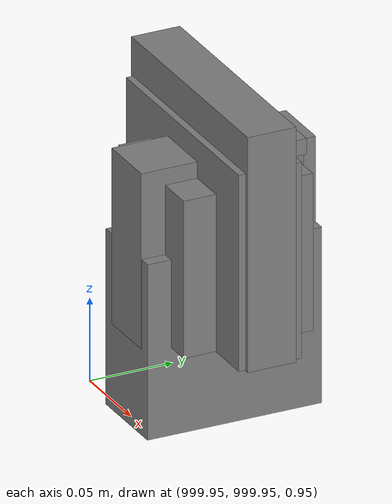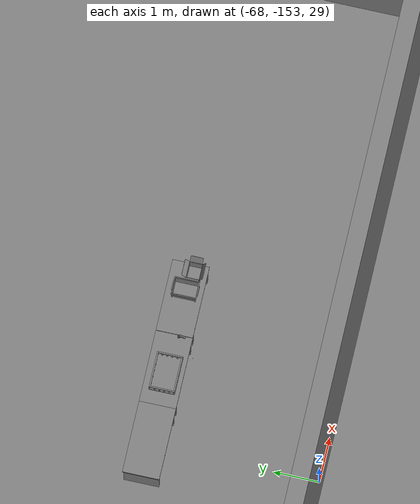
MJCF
<mujoco>
    <option gravity="0.000000000 0.000000000 -9.810000420" timestep="0.0049999999" integrator="implicitfast" density="1.225" viscosity="1.8000001e-05" noslip_iterations="10" iterations="100" sdf_iterations="50">
        <flag multiccd="disable"/>
    </option>
    <size memory="1000M"/>
    <compiler coordinate="local"/>
    <worldbody>
        <light cutoff="30" pos="0 1 1" dir="0 -1 -2"/>
        <light cutoff="30" pos="0 -1 1" dir="0 1 -2"/>
        <body pos="-64.866622925 -149.383972168 30.183746338" euler="89.999984741 89.999946594 0.000000000" name="openloong_gripper_2f85_fix_base_usda_bluebox_01">
            <geom contype="1" conaffinity="1" density="1000" type="box" material="" rgba="0.500000000 0.500000000 0.500000000 1.000000000" solimp="0.899999976 0.949999988 0.001000000" friction="1.000000000 0.005000000 0.000100000" solref="0.020000000 1.000000000" margin="0" condim="3" group="0" pos="0.276580811 0.187225342 0.000068665" quat="0.707106948 0.000077471 0.707106352 0.000077486" size="0.100000001 0.057999998 0.010000000" name="openloong_gripper_2f85_fix_base_usda_geom_7F3FE64C_9C68_4DF6_93F2_6EDD397E486B"/>
            <geom contype="1" conaffinity="1" density="1000" type="box" material="" rgba="0.500000000 0.500000000 0.500000000 1.000000000" solimp="0.899999976 0.949999988 0.001000000" friction="1.000000000 0.005000000 0.000100000" solref="0.020000000 1.000000000" margin="0" condim="3" group="0" pos="0.000000000 0.002883911 0.000000000" quat="0.999999881 0.000000000 0.000000000 0.000000000" size="0.254000008 0.003000000 0.172000006" name="openloong_gripper_2f85_fix_base_usda_geom_76259964_D083_4C97_8C4D_6C8A1E6E24ED"/>
            <geom contype="1" conaffinity="1" density="1000" type="box" material="" rgba="0.500000000 0.500000000 0.500000000 1.000000000" solimp="0.899999976 0.949999988 0.001000000" friction="1.000000000 0.005000000 0.000100000" solref="0.020000000 1.000000000" margin="0" condim="3" group="0" pos="0.000000000 0.124874115 0.173484802" quat="0.999796331 0.020176515 -0.000000015 0.000000030" size="0.259999990 0.119999997 0.007000000" name="openloong_gripper_2f85_fix_base_usda_geom_8F0C616B_E094_41DF_B8C9_0FD8783509ED"/>
            <geom contype="1" conaffinity="1" density="1000" type="box" material="" rgba="0.500000000 0.500000000 0.500000000 1.000000000" solimp="0.899999976 0.949999988 0.001000000" friction="1.000000000 0.005000000 0.000100000" solref="0.020000000 1.000000000" margin="0" condim="3" group="0" pos="0.000000000 0.124874115 -0.173469543" quat="0.999796331 -0.020176545 -0.000000015 0.000000000" size="0.259999990 0.119999997 0.007000000" name="openloong_gripper_2f85_fix_base_usda_geom_757AC6F3_BB43_4F64_B3E9_8C2F04082590"/>
            <geom contype="1" conaffinity="1" density="1000" type="box" material="" rgba="0.500000000 0.500000000 0.500000000 1.000000000" solimp="0.899999976 0.949999988 0.001000000" friction="1.000000000 0.005000000 0.000100000" solref="0.020000000 1.000000000" margin="0" condim="3" group="0" pos="0.000000000 0.214008331 0.188980103" quat="0.999912977 0.013176724 0.000000015 0.000000000" size="0.259999990 0.029999999 0.012500000" name="openloong_gripper_2f85_fix_base_usda_geom_6D861102_6B47_48D9_9E46_9BECB03E4293"/>
            <geom contype="1" conaffinity="1" density="1000" type="box" material="" rgba="0.500000000 0.500000000 0.500000000 1.000000000" solimp="0.899999976 0.949999988 0.001000000" friction="1.000000000 0.005000000 0.000100000" solref="0.020000000 1.000000000" margin="0" condim="3" group="0" pos="-0.258361816 0.125289917 0.001876831" quat="0.702796936 -0.020792112 0.710783124 0.020769298" size="0.189999998 0.119999997 0.009000000" name="openloong_gripper_2f85_fix_base_usda_geom_D5C7CDB2_B76A_4A79_A761_CEC3291D9AE0"/>
            <geom contype="1" conaffinity="1" density="1000" type="box" material="" rgba="0.500000000 0.500000000 0.500000000 1.000000000" solimp="0.899999976 0.949999988 0.001000000" friction="1.000000000 0.005000000 0.000100000" solref="0.020000000 1.000000000" margin="0" condim="3" group="0" pos="0.000000000 0.214008331 -0.188980103" quat="0.999912977 -0.013176769 0.000000030 0.000000015" size="0.259999990 0.029999999 0.012500000" name="openloong_gripper_2f85_fix_base_usda_geom_06A24FF9_C623_479E_BD51_0B408D532CF8"/>
            <geom contype="1" conaffinity="1" density="1000" type="box" material="" rgba="0.500000000 0.500000000 0.500000000 1.000000000" solimp="0.899999976 0.949999988 0.001000000" friction="1.000000000 0.005000000 0.000100000" solref="0.020000000 1.000000000" margin="0" condim="3" group="0" pos="-0.276611328 0.187225342 0.000068665" quat="0.707106650 0.000077441 0.707106709 0.000077456" size="0.100000001 0.057999998 0.010000000" name="openloong_gripper_2f85_fix_base_usda_geom_3A62D227_8E5F_44B8_A4A3_B3E98715DBB2"/>
            <geom contype="1" conaffinity="1" density="1000" type="box" material="" rgba="0.500000000 0.500000000 0.500000000 1.000000000" solimp="0.899999976 0.949999988 0.001000000" friction="1.000000000 0.005000000 0.000100000" solref="0.020000000 1.000000000" margin="0" condim="3" group="0" pos="0.258331299 0.125289917 0.001876831" quat="0.702851415 0.018856421 0.710823774 -0.019329369" size="0.189999998 0.119999997 0.009000000" name="openloong_gripper_2f85_fix_base_usda_geom_9A34FD74_740D_4E6F_A24B_CC29E1320555"/>
            <freejoint name="openloong_gripper_2f85_fix_base_usda_bluebox_01_joint"/>
            <site size="0.005000000 0.005000000 0.005000000" rgba="0.500000000 0.500000000 0.500000000 1.000000000" pos="0.000000000 0.000000000 0.000000000" quat="0.999961913 0.008726534 0.000000000 0.000000000" group="0" type="sphere" name="openloong_gripper_2f85_fix_base_usda_bluebox_01site"/>
        </body>
        <body pos="-64.496299744 -149.491867065 30.235729218" euler="0.000000000 0.000000000 89.999946594" name="openloong_gripper_2f85_fix_base_usda_cardboardbox_01">
            <geom contype="1" conaffinity="1" density="1000" type="box" material="" rgba="0.500000000 0.500000000 0.500000000 1.000000000" solimp="0.899999976 0.949999988 0.001000000" friction="1.000000000 0.005000000 0.000100000" solref="0.020000000 1.000000000" margin="0" condim="3" group="0" pos="-0.003166199 -0.004086494 0.005052090" quat="1.000000000 0.000000000 0.000000000 0.000000000" size="0.142499998 0.177500010 0.005000000" name="openloong_gripper_2f85_fix_base_usda_geom_3A6C1BBD_F8D1_48C9_8755_59EE021592E2"/>
            <geom contype="1" conaffinity="1" density="1000" type="box" material="" rgba="0.500000000 0.500000000 0.500000000 1.000000000" solimp="0.899999976 0.949999988 0.001000000" friction="1.000000000 0.005000000 0.000100000" solref="0.020000000 1.000000000" margin="0" condim="3" group="0" pos="-0.003166199 0.170316696 0.150570869" quat="1.000000000 0.000000000 0.000000000 0.000000000" size="0.142499998 0.005000000 0.149999991" name="openloong_gripper_2f85_fix_base_usda_geom_72CE084A_9B35_47C3_9745_6224E436A834"/>
            <geom contype="1" conaffinity="1" density="1000" type="box" material="" rgba="0.500000000 0.500000000 0.500000000 1.000000000" solimp="0.899999976 0.949999988 0.001000000" friction="1.000000000 0.005000000 0.000100000" solref="0.020000000 1.000000000" margin="0" condim="3" group="0" pos="-0.147399902 -0.005307198 0.150570869" quat="1.000000000 0.000000000 0.000000000 0.000000000" size="0.005000000 0.177500010 0.149999991" name="openloong_gripper_2f85_fix_base_usda_geom_A4E000B5_0DFE_45F2_AB8C_BE6D6C37E1F4"/>
            <geom contype="1" conaffinity="1" density="1000" type="box" material="" rgba="0.500000000 0.500000000 0.500000000 1.000000000" solimp="0.899999976 0.949999988 0.001000000" friction="1.000000000 0.005000000 0.000100000" solref="0.020000000 1.000000000" margin="0" condim="3" group="0" pos="0.140275955 -0.005307198 0.150570869" quat="1.000000000 0.000000000 0.000000000 0.000000000" size="0.005000000 0.177500010 0.149999991" name="openloong_gripper_2f85_fix_base_usda_geom_D0F5B6E7_EAEE_49BA_9352_4905E0F10C77"/>
            <geom contype="1" conaffinity="1" density="1000" type="box" material="" rgba="0.500000000 0.500000000 0.500000000 1.000000000" solimp="0.899999976 0.949999988 0.001000000" friction="1.000000000 0.005000000 0.000100000" solref="0.020000000 1.000000000" margin="0" condim="3" group="0" pos="-0.003166199 -0.181550980 0.150570869" quat="1.000000000 0.000000000 0.000000000 0.000000000" size="0.142499998 0.005000000 0.149999991" name="openloong_gripper_2f85_fix_base_usda_geom_92E41CC9_71DA_4FA9_ABCE_6CA8590739A6"/>
            <freejoint name="openloong_gripper_2f85_fix_base_usda_cardboardbox_01_joint"/>
            <site size="0.005000000 0.005000000 0.005000000" rgba="0.500000000 0.500000000 0.500000000 1.000000000" pos="0.000000000 0.000000000 0.000000000" quat="0.999961913 0.008726535 0.000000000 0.000000000" group="0" type="sphere" name="openloong_gripper_2f85_fix_base_usda_site_9B144023_44D0_4115_AF16_4EDDA99FE223"/>
            <body pos="0.139160156 -0.004048347 0.301930904" euler="-179.999954224 49.383502960 179.999954224" name="openloong_gripper_2f85_fix_base_usda_A1_006">
                <geom contype="1" conaffinity="1" density="1000" type="box" material="" rgba="0.500000000 0.500000000 0.500000000 1.000000000" solimp="0.899999976 0.949999988 0.001000000" friction="1.000000000 0.005000000 0.000100000" solref="0.020000000 1.000000000" margin="0" condim="3" group="0" pos="-0.071587563 0.000009537 0.001745224" quat="0.999999881 0.000000000 0.000000000 0.000000000" size="0.071249999 0.179999992 0.002500000" name="openloong_gripper_2f85_fix_base_usda_geom_E44415F8_26AB_436F_8D54_548F32FF4A22"/>
                <joint armature="0" stiffness="0.07" damping="0.0099999998" axis="0.000000 1.000000 0.000000" type="hinge" name="openloong_gripper_2f85_fix_base_usda_A1_006"/>
            </body>
            <body pos="-0.145902634 -0.004086494 0.301938057" euler="-180.000000000 -60.000011444 -180.000000000" name="openloong_gripper_2f85_fix_base_usda_A2_006">
                <geom contype="1" conaffinity="1" density="1000" type="box" material="" rgba="0.500000000 0.500000000 0.500000000 1.000000000" solimp="0.899999976 0.949999988 0.001000000" friction="1.000000000 0.005000000 0.000100000" solref="0.020000000 1.000000000" margin="0" condim="3" group="0" pos="0.071268082 0.000009537 0.002717972" quat="0.000002921 0.000000000 -0.000000030 0.999999881" size="0.071249999 0.179999992 0.002500000" name="openloong_gripper_2f85_fix_base_usda_geom_478B183E_4007_4D4C_830E_9C317BBA440A"/>
                <joint armature="0" stiffness="0.07" damping="0.0099999998" axis="0.000000 1.000000 0.000000" type="hinge" name="openloong_gripper_2f85_fix_base_usda_A2_006"/>
            </body>
            <body pos="-0.003385544 0.175991058 0.301930904" euler="-125.858116150 -0.000004561 0.000002331" name="openloong_gripper_2f85_fix_base_usda_B2_006">
                <geom contype="1" conaffinity="1" density="1000" type="box" material="" rgba="0.500000000 0.500000000 0.500000000 1.000000000" solimp="0.899999976 0.949999988 0.001000000" friction="1.000000000 0.005000000 0.000100000" solref="0.020000000 1.000000000" margin="0" condim="3" group="0" pos="0.000009537 -0.070939064 -0.002470016" quat="0.999614120 0.027776197 -0.000000015 0.000000030" size="0.137500003 0.064999998 0.005000000" name="openloong_gripper_2f85_fix_base_usda_geom_E7C47AF2_D490_40FC_BDCC_54FE45C99487"/>
                <joint armature="0" stiffness="0.07" damping="0.0099999998" axis="1.000000 0.000000 0.000000" type="hinge" name="openloong_gripper_2f85_fix_base_usda_B2_006"/>
            </body>
            <body pos="-0.003385544 -0.184140205 0.301938057" euler="147.805557251 0.000000000 0.000000000" name="openloong_gripper_2f85_fix_base_usda_B1_006">
                <geom contype="1" conaffinity="1" density="1000" type="box" material="" rgba="0.500000000 0.500000000 0.500000000 1.000000000" solimp="0.899999976 0.949999988 0.001000000" friction="1.000000000 0.005000000 0.000100000" solref="0.020000000 1.000000000" margin="0" condim="3" group="0" pos="-0.000028610 0.070202351 -0.002703667" quat="0.999614179 -0.027776167 0.000000000 0.000000000" size="0.137500003 0.064999998 0.005000000" name="openloong_gripper_2f85_fix_base_usda_geom_869477D8_69CC_4649_9858_F1179DA8D7ED"/>
                <joint armature="0" stiffness="0.07" damping="0.0099999998" axis="1.000000 0.000000 0.000000" type="hinge" name="openloong_gripper_2f85_fix_base_usda_B1_006"/>
            </body>
        </body>
        <body pos="-65.882858276 -149.481979370 30.229999542" euler="-64.487716675 0.000000000 0.000000000" name="openloong_gripper_2f85_fix_base_usda_Barcode">
            <geom contype="1" conaffinity="1" density="1000" type="box" material="" rgba="0.500000000 0.500000000 0.500000000 1.000000000" solimp="0.899999976 0.949999988 0.001000000" friction="1.000000000 0.005000000 0.000100000" solref="0.020000000 1.000000000" margin="0" condim="3" group="0" pos="0.000000000 0.013038635 0.001419067" quat="0.000000000 0.000000000 0.000000000 1.000000119" size="0.034000002 0.010000000 0.017999999" name="openloong_gripper_2f85_fix_base_usda_geom_EFBEEEC0_1D1D_41AF_A499_B653E5FA0084"/>
            <geom contype="1" conaffinity="1" density="1000" type="box" material="" rgba="0.500000000 0.500000000 0.500000000 1.000000000" solimp="0.899999976 0.949999988 0.001000000" friction="1.000000000 0.005000000 0.000100000" solref="0.020000000 1.000000000" margin="0" condim="3" group="0" pos="0.000000000 -0.035301208 -0.007095337" quat="0.000000000 0.000000000 -0.043619365 0.999048233" size="0.028999999 0.010000000 0.020000000" name="openloong_gripper_2f85_fix_base_usda_geom_717673B3_7F66_4BD0_B879_FAB011E3E1AD"/>
            <geom contype="1" conaffinity="1" density="1000" type="box" material="" rgba="0.500000000 0.500000000 0.500000000 1.000000000" solimp="0.899999976 0.949999988 0.001000000" friction="1.000000000 0.005000000 0.000100000" solref="0.020000000 1.000000000" margin="0" condim="3" group="0" pos="0.000000000 -0.043411255 -0.011749268" quat="0.922262907 0.386563420 0.000000000 0.000000000" size="0.026000001 0.010000000 0.020000000" name="openloong_gripper_2f85_fix_base_usda_geom_57093FF8_AC55_42CE_B0F8_E6136FBCC38B"/>
            <geom contype="1" conaffinity="1" density="1000" type="box" material="" rgba="0.500000000 0.500000000 0.500000000 1.000000000" solimp="0.899999976 0.949999988 0.001000000" friction="1.000000000 0.005000000 0.000100000" solref="0.020000000 1.000000000" margin="0" condim="3" group="0" pos="0.000000000 -0.016967773 -0.031860352" quat="0.000000000 0.000000000 0.000000000 1.000000119" size="0.008000000 0.010000000 0.013000000" name="openloong_gripper_2f85_fix_base_usda_geom_E14EAC78_473E_4A5A_83C1_C16018D11421"/>
            <geom contype="1" conaffinity="1" density="1000" type="box" material="" rgba="0.500000000 0.500000000 0.500000000 1.000000000" solimp="0.899999976 0.949999988 0.001000000" friction="1.000000000 0.005000000 0.000100000" solref="0.020000000 1.000000000" margin="0" condim="3" group="0" pos="0.000000000 -0.001869202 0.000312805" quat="0.953716993 0.300705761 0.000000000 0.000000000" size="0.032000002 0.010000000 0.018999999" name="openloong_gripper_2f85_fix_base_usda_geom_A66B7083_1C63_41CA_A3B6_6BFD9E83C594"/>
            <geom contype="1" conaffinity="1" density="1000" type="box" material="" rgba="0.500000000 0.500000000 0.500000000 1.000000000" solimp="0.899999976 0.949999988 0.001000000" friction="1.000000000 0.005000000 0.000100000" solref="0.020000000 1.000000000" margin="0" condim="3" group="0" pos="0.000000000 -0.019531250 -0.003173828" quat="0.953716993 0.300705761 0.000000000 0.000000000" size="0.030999999 0.010000000 0.020000000" name="openloong_gripper_2f85_fix_base_usda_geom_8F8D9232_34A2_42E5_9683_056DC99E6607"/>
            <geom contype="1" conaffinity="1" density="1000" type="box" material="" rgba="0.500000000 0.500000000 0.500000000 1.000000000" solimp="0.899999976 0.949999988 0.001000000" friction="1.000000000 0.005000000 0.000100000" solref="0.020000000 1.000000000" margin="0" condim="3" group="0" pos="0.000000000 -0.035301208 -0.007095337" quat="0.953716993 0.300705761 0.000000000 0.000000000" size="0.028999999 0.010000000 0.020000000" name="openloong_gripper_2f85_fix_base_usda_geom_80E202D6_BB66_4F0D_A66E_A8B83A775AAD"/>
            <geom contype="1" conaffinity="1" density="1000" type="box" material="" rgba="0.500000000 0.500000000 0.500000000 1.000000000" solimp="0.899999976 0.949999988 0.001000000" friction="1.000000000 0.005000000 0.000100000" solref="0.020000000 1.000000000" margin="0" condim="3" group="0" pos="0.000000000 -0.042617798 -0.071121216" quat="0.000000000 0.000000000 0.000000000 1.000000119" size="0.013000000 0.021000000 0.059999999" name="openloong_gripper_2f85_fix_base_usda_geom_B5613F07_E2C8_4AB3_B92E_9B8A948BD5CC"/>
            <freejoint name="openloong_gripper_2f85_fix_base_usda_Barcode_joint"/>
            <site size="0.005000000 0.005000000 0.005000000" rgba="0.500000000 0.500000000 0.500000000 1.000000000" pos="0.000000000 0.000000000 0.000000000" quat="1.000000000 0.000000000 0.000000000 0.000000000" group="0" type="sphere" name="openloong_gripper_2f85_fix_base_usda_Barcode_site"/>
        </body>
        <body pos="-66.745018005 -149.392349243 30.184000015" euler="0.000000000 0.000000000 89.999946594" name="[22329797567401]_Basket_01">
            <geom contype="1" conaffinity="1" density="1000" type="box" material="" rgba="0.500000000 0.500000000 0.500000000 1.000000000" solimp="0.899999976 0.949999988 0.001000000" friction="1.000000000 0.005000000 0.000100000" solref="0.020000000 1.000000000" margin="0" condim="3" group="0" pos="-0.052425385 0.389207840 0.089787483" quat="0.707107008 0.000000000 0.000000000 0.707106411" size="0.014249999 0.014249999 0.059999999" name="[22329797567401]_geom_9EA045C0_584F_4462_B6B7_2B283419EB05"/>
            <geom contype="1" conaffinity="1" density="1000" type="box" material="" rgba="0.500000000 0.500000000 0.500000000 1.000000000" solimp="0.899999976 0.949999988 0.001000000" friction="1.000000000 0.005000000 0.000100000" solref="0.020000000 1.000000000" margin="0" condim="3" group="0" pos="0.264015198 -0.133043289 0.089787483" quat="0.707107008 0.000000000 0.000000000 0.707106411" size="0.014249999 0.014249999 0.059999999" name="[22329797567401]_geom_2BCC38FD_8582_4B99_BBB7_45A48289B6E5"/>
            <geom contype="1" conaffinity="1" density="1000" type="box" material="" rgba="0.500000000 0.500000000 0.500000000 1.000000000" solimp="0.899999976 0.949999988 0.001000000" friction="1.000000000 0.005000000 0.000100000" solref="0.020000000 1.000000000" margin="0" condim="3" group="0" pos="-0.264015198 -0.265548706 0.089793205" quat="0.707107008 0.000000000 0.000000000 0.707106411" size="0.014249999 0.014249999 0.059999999" name="[22329797567401]_geom_82A712C6_CCC0_4D56_A638_80134380E63F"/>
            <geom contype="1" conaffinity="1" density="1000" type="box" material="" rgba="0.500000000 0.500000000 0.500000000 1.000000000" solimp="0.899999976 0.949999988 0.001000000" friction="1.000000000 0.005000000 0.000100000" solref="0.020000000 1.000000000" margin="0" condim="3" group="0" pos="-0.160263062 -0.389322281 0.089793205" quat="0.707107008 0.000000000 0.000000000 0.707106411" size="0.014249999 0.014249999 0.059999999" name="[22329797567401]_geom_AEB743BF_23DB_4A54_8751_AA6CCFDFBF76"/>
            <geom contype="1" conaffinity="1" density="1000" type="box" material="" rgba="0.500000000 0.500000000 0.500000000 1.000000000" solimp="0.899999976 0.949999988 0.001000000" friction="1.000000000 0.005000000 0.000100000" solref="0.020000000 1.000000000" margin="0" condim="3" group="0" pos="0.162265778 -0.389322281 0.089787483" quat="0.707107008 0.000000000 0.000000000 0.707106411" size="0.014249999 0.014249999 0.059999999" name="[22329797567401]_geom_5B996AE3_9A68_4A69_8A2A_6B8F56886179"/>
            <geom contype="1" conaffinity="1" density="1000" type="box" material="" rgba="0.500000000 0.500000000 0.500000000 1.000000000" solimp="0.899999976 0.949999988 0.001000000" friction="1.000000000 0.005000000 0.000100000" solref="0.020000000 1.000000000" margin="0" condim="3" group="0" pos="0.264015198 0.389207840 0.089787483" quat="0.707107008 0.000000000 0.000000000 0.707106411" size="0.014249999 0.014249999 0.059999999" name="[22329797567401]_geom_690D5EB9_4654_47B0_A71A_EB300E0AFA1A"/>
            <geom contype="1" conaffinity="1" density="1000" type="box" material="" rgba="0.500000000 0.500000000 0.500000000 1.000000000" solimp="0.899999976 0.949999988 0.001000000" friction="1.000000000 0.005000000 0.000100000" solref="0.020000000 1.000000000" margin="0" condim="3" group="0" pos="-0.264015198 -0.133043289 0.089793205" quat="0.707107008 0.000000000 0.000000000 0.707106411" size="0.014249999 0.014249999 0.059999999" name="[22329797567401]_geom_2EF8E910_0850_477D_9BCB_8A0234D56AC5"/>
            <geom contype="1" conaffinity="1" density="1000" type="box" material="" rgba="0.500000000 0.500000000 0.500000000 1.000000000" solimp="0.899999976 0.949999988 0.001000000" friction="1.000000000 0.005000000 0.000100000" solref="0.020000000 1.000000000" margin="0" condim="3" group="0" pos="-0.264026642 0.269256592 0.089793205" quat="0.707107008 0.000000000 0.000000000 0.707106411" size="0.014249999 0.014249999 0.059999999" name="[22329797567401]_geom_A3DE40FA_6BA6_45D2_9507_5B48AA8BDB6E"/>
            <geom contype="1" conaffinity="1" density="1000" type="box" material="" rgba="0.500000000 0.500000000 0.500000000 1.000000000" solimp="0.899999976 0.949999988 0.001000000" friction="1.000000000 0.005000000 0.000100000" solref="0.020000000 1.000000000" margin="0" condim="3" group="0" pos="0.054462433 0.389207840 0.089787483" quat="0.707107008 0.000000000 0.000000000 0.707106411" size="0.014249999 0.014249999 0.059999999" name="[22329797567401]_geom_33E80DAA_2A08_4B05_9F7D_11A2612F59D4"/>
            <geom contype="1" conaffinity="1" density="1000" type="box" material="" rgba="0.500000000 0.500000000 0.500000000 1.000000000" solimp="0.899999976 0.949999988 0.001000000" friction="1.000000000 0.005000000 0.000100000" solref="0.020000000 1.000000000" margin="0" condim="3" group="0" pos="0.054462433 -0.389322281 0.089787483" quat="0.707107008 0.000000000 0.000000000 0.707106411" size="0.014249999 0.014249999 0.059999999" name="[22329797567401]_geom_D72503C6_7E09_4A5D_B9ED_47ED76901C51"/>
            <geom contype="1" conaffinity="1" density="1000" type="box" material="" rgba="0.500000000 0.500000000 0.500000000 1.000000000" solimp="0.899999976 0.949999988 0.001000000" friction="1.000000000 0.005000000 0.000100000" solref="0.020000000 1.000000000" margin="0" condim="3" group="0" pos="0.264015198 0.269256592 0.089793205" quat="0.707107008 0.000000000 0.000000000 0.707106411" size="0.014249999 0.014249999 0.059999999" name="[22329797567401]_geom_B20E9010_59EF_4B33_BB6D_69529A8BE7BC"/>
            <geom contype="1" conaffinity="1" density="1000" type="box" material="" rgba="0.500000000 0.500000000 0.500000000 1.000000000" solimp="0.899999976 0.949999988 0.001000000" friction="1.000000000 0.005000000 0.000100000" solref="0.020000000 1.000000000" margin="0" condim="3" group="0" pos="0.264015198 -0.389322281 0.089787483" quat="0.707107008 0.000000000 0.000000000 0.707106411" size="0.014249999 0.014249999 0.059999999" name="[22329797567401]_geom_C7C83A66_D500_4495_95D0_97176B9EA1A1"/>
            <geom contype="1" conaffinity="1" density="1000" type="box" material="" rgba="0.500000000 0.500000000 0.500000000 1.000000000" solimp="0.899999976 0.949999988 0.001000000" friction="1.000000000 0.005000000 0.000100000" solref="0.020000000 1.000000000" margin="0" condim="3" group="0" pos="0.000000000 0.000000000 0.015998840" quat="0.707107008 0.000000000 0.000000000 0.707106411" size="0.403499991 0.279000014 0.015750000" name="[22329797567401]_geom_EC10E7AC_9509_4244_BC36_3E40E4221DFB"/>
            <geom contype="1" conaffinity="1" density="1000" type="box" material="" rgba="0.500000000 0.500000000 0.500000000 1.000000000" solimp="0.899999976 0.949999988 0.001000000" friction="1.000000000 0.005000000 0.000100000" solref="0.020000000 1.000000000" margin="0" condim="3" group="0" pos="0.000000000 -0.389476776 0.163619041" quat="0.707107008 0.000000000 0.000000000 0.707106411" size="0.015000000 0.277500004 0.015750000" name="[22329797567401]_geom_FAAF24F2_3453_43D9_98BC_AE5421BD23D2"/>
            <geom contype="1" conaffinity="1" density="1000" type="box" material="" rgba="0.500000000 0.500000000 0.500000000 1.000000000" solimp="0.899999976 0.949999988 0.001000000" friction="1.000000000 0.005000000 0.000100000" solref="0.020000000 1.000000000" margin="0" condim="3" group="0" pos="0.162265778 0.389207840 0.089787483" quat="0.707107008 0.000000000 0.000000000 0.707106411" size="0.014249999 0.014249999 0.059999999" name="[22329797567401]_geom_B971BDA1_DEDF_425E_B6B4_14E152A23C61"/>
            <geom contype="1" conaffinity="1" density="1000" type="box" material="" rgba="0.500000000 0.500000000 0.500000000 1.000000000" solimp="0.899999976 0.949999988 0.001000000" friction="1.000000000 0.005000000 0.000100000" solref="0.020000000 1.000000000" margin="0" condim="3" group="0" pos="0.000000000 0.389471054 0.163619041" quat="0.707107008 0.000000000 0.000000000 0.707106411" size="0.015000000 0.277500004 0.015750000" name="[22329797567401]_geom_67F01CE2_C164_4BCC_9595_F6B53835495C"/>
            <geom contype="1" conaffinity="1" density="1000" type="box" material="" rgba="0.500000000 0.500000000 0.500000000 1.000000000" solimp="0.899999976 0.949999988 0.001000000" friction="1.000000000 0.005000000 0.000100000" solref="0.020000000 1.000000000" margin="0" condim="3" group="0" pos="-0.263511658 0.000000000 0.163619041" quat="0.707107008 0.000000000 0.000000000 0.707106411" size="0.403499991 0.015000000 0.015750000" name="[22329797567401]_geom_4C9C25BC_B5B2_4102_ADAF_F97FE714E728"/>
            <geom contype="1" conaffinity="1" density="1000" type="box" material="" rgba="0.500000000 0.500000000 0.500000000 1.000000000" solimp="0.899999976 0.949999988 0.001000000" friction="1.000000000 0.005000000 0.000100000" solref="0.020000000 1.000000000" margin="0" condim="3" group="0" pos="-0.264015198 0.141334534 0.089793205" quat="0.707107008 0.000000000 0.000000000 0.707106411" size="0.014249999 0.014249999 0.059999999" name="[22329797567401]_geom_3CDEB8F1_9CCC_484A_943D_13342D2BA5AD"/>
            <geom contype="1" conaffinity="1" density="1000" type="box" material="" rgba="0.500000000 0.500000000 0.500000000 1.000000000" solimp="0.899999976 0.949999988 0.001000000" friction="1.000000000 0.005000000 0.000100000" solref="0.020000000 1.000000000" margin="0" condim="3" group="0" pos="0.264015198 -0.265548706 0.089787483" quat="0.707107008 0.000000000 0.000000000 0.707106411" size="0.014249999 0.014249999 0.059999999" name="[22329797567401]_geom_57437646_2775_4E51_BF0C_4768D73E952D"/>
            <geom contype="1" conaffinity="1" density="1000" type="box" material="" rgba="0.500000000 0.500000000 0.500000000 1.000000000" solimp="0.899999976 0.949999988 0.001000000" friction="1.000000000 0.005000000 0.000100000" solref="0.020000000 1.000000000" margin="0" condim="3" group="0" pos="-0.160263062 0.389207840 0.089787483" quat="0.707107008 0.000000000 0.000000000 0.707106411" size="0.014249999 0.014249999 0.059999999" name="[22329797567401]_geom_47AA07AC_AC86_4A1C_9095_9B09509FA4B6"/>
            <geom contype="1" conaffinity="1" density="1000" type="box" material="" rgba="0.500000000 0.500000000 0.500000000 1.000000000" solimp="0.899999976 0.949999988 0.001000000" friction="1.000000000 0.005000000 0.000100000" solref="0.020000000 1.000000000" margin="0" condim="3" group="0" pos="-0.052425385 -0.389322281 0.089787483" quat="0.707107008 0.000000000 0.000000000 0.707106411" size="0.014249999 0.014249999 0.059999999" name="[22329797567401]_geom_4CCD901A_69A7_47F0_9B56_C1FC4CCDD832"/>
            <geom contype="1" conaffinity="1" density="1000" type="box" material="" rgba="0.500000000 0.500000000 0.500000000 1.000000000" solimp="0.899999976 0.949999988 0.001000000" friction="1.000000000 0.005000000 0.000100000" solref="0.020000000 1.000000000" margin="0" condim="3" group="0" pos="-0.264026642 -0.389322281 0.089793205" quat="0.707107008 0.000000000 0.000000000 0.707106411" size="0.014249999 0.014249999 0.059999999" name="[22329797567401]_geom_5D74853D_1DB0_4B93_8C3C_EDD97C9F0738"/>
            <geom contype="1" conaffinity="1" density="1000" type="box" material="" rgba="0.500000000 0.500000000 0.500000000 1.000000000" solimp="0.899999976 0.949999988 0.001000000" friction="1.000000000 0.005000000 0.000100000" solref="0.020000000 1.000000000" margin="0" condim="3" group="0" pos="0.264015198 0.141334534 0.089787483" quat="0.707107008 0.000000000 0.000000000 0.707106411" size="0.014249999 0.014249999 0.059999999" name="[22329797567401]_geom_377C7514_E199_46EA_A649_E327217CCB09"/>
            <geom contype="1" conaffinity="1" density="1000" type="box" material="" rgba="0.500000000 0.500000000 0.500000000 1.000000000" solimp="0.899999976 0.949999988 0.001000000" friction="1.000000000 0.005000000 0.000100000" solref="0.020000000 1.000000000" margin="0" condim="3" group="0" pos="-0.264015198 0.389207840 0.089793205" quat="0.707107008 0.000000000 0.000000000 0.707106411" size="0.014249999 0.014249999 0.059999999" name="[22329797567401]_geom_43403DB3_B03E_480C_830B_C8438B0DCB93"/>
            <geom contype="1" conaffinity="1" density="1000" type="box" material="" rgba="0.500000000 0.500000000 0.500000000 1.000000000" solimp="0.899999976 0.949999988 0.001000000" friction="1.000000000 0.005000000 0.000100000" solref="0.020000000 1.000000000" margin="0" condim="3" group="0" pos="0.264015198 0.004480362 0.089787483" quat="0.707107008 0.000000000 0.000000000 0.707106411" size="0.014249999 0.014249999 0.059999999" name="[22329797567401]_geom_A417334A_BF4E_47B5_A914_67976EFE08C2"/>
            <geom contype="1" conaffinity="1" density="1000" type="box" material="" rgba="0.500000000 0.500000000 0.500000000 1.000000000" solimp="0.899999976 0.949999988 0.001000000" friction="1.000000000 0.005000000 0.000100000" solref="0.020000000 1.000000000" margin="0" condim="3" group="0" pos="0.263694763 -0.000011444 0.163619041" quat="0.707107008 0.000000000 0.000000000 0.707106411" size="0.403499991 0.015000000 0.015750000" name="[22329797567401]_geom_A46B77F1_DFC1_41F5_9870_68526FAF48F3"/>
            <geom contype="1" conaffinity="1" density="1000" type="box" material="" rgba="0.500000000 0.500000000 0.500000000 1.000000000" solimp="0.899999976 0.949999988 0.001000000" friction="1.000000000 0.005000000 0.000100000" solref="0.020000000 1.000000000" margin="0" condim="3" group="0" pos="-0.264015198 0.004480362 0.089793205" quat="0.707107008 0.000000000 0.000000000 0.707106411" size="0.014249999 0.014249999 0.059999999" name="[22329797567401]_geom_97BA0235_4213_4501_9D2A_E1CE133C018D"/>
            <freejoint name="[22329797567401]_joint_B9670814_3F35_4540_A552_06ED3137BF9F"/>
        </body>
        <body pos="0.000000000 0.000000000 0.000000000" euler="0.000000000 0.000000000 0.000000000" name="Static Objects_Static Objects">
            <geom contype="1" conaffinity="1" density="1000" type="box" material="" rgba="0.500000000 0.500000000 0.500000000 1.000000000" solimp="0.899999976 0.949999988 0.001000000" friction="1.000000000 0.005000000 0.000100000" solref="0.020000000 1.000000000" margin="0" condim="3" group="0" pos="-67.544113159 -149.365814209 29.727830887" quat="0.500000417 0.499999970 0.499999553 0.499999970" size="0.381000012 0.319999993 0.041000001" name="Static Objects_geom_4288A877_0FBE_4E9F_BF97_CFC7BB55CB83"/>
            <geom contype="1" conaffinity="1" density="1000" type="box" material="" rgba="0.500000000 0.500000000 0.500000000 1.000000000" solimp="0.899999976 0.949999988 0.001000000" friction="1.000000000 0.005000000 0.000100000" solref="0.020000000 1.000000000" margin="0" condim="3" group="0" pos="-68.239501953 -149.365814209 30.086868286" quat="0.500000417 0.499999970 0.499999553 0.499999970" size="0.370999992 0.039500002 0.745000005" name="Static Objects_geom_C3424226_121A_40EA_A0AE_B93048C3B9CD"/>
            <geom contype="1" conaffinity="1" density="1000" type="box" material="" rgba="0.500000000 0.500000000 0.500000000 1.000000000" solimp="0.899999976 0.949999988 0.001000000" friction="1.000000000 0.005000000 0.000100000" solref="0.020000000 1.000000000" margin="0" condim="3" group="0" pos="-68.239501953 -149.365814209 30.147235870" quat="0.500000417 0.499999970 0.499999553 0.499999970" size="0.400000006 0.022000000 0.800000012" name="Static Objects_geom_16E85CE5_F270_41E5_A117_8E3213545717"/>
            <geom contype="1" conaffinity="1" density="1000" type="box" material="" rgba="0.500000000 0.500000000 0.500000000 1.000000000" solimp="0.899999976 0.949999988 0.001000000" friction="1.000000000 0.005000000 0.000100000" solref="0.020000000 1.000000000" margin="0" condim="3" group="0" pos="-68.934890747 -149.365814209 29.727830887" quat="0.500000417 0.499999970 0.499999553 0.499999970" size="0.381000012 0.319999993 0.041000001" name="Static Objects_geom_405F1F8C_64B7_42E0_8EB8_87EF3D6E88D2"/>
            <geom contype="1" conaffinity="1" density="1000" type="box" material="" rgba="0.500000000 0.500000000 0.500000000 1.000000000" solimp="0.899999976 0.949999988 0.001000000" friction="1.000000000 0.005000000 0.000100000" solref="0.020000000 1.000000000" margin="0" condim="3" group="0" pos="-68.239501953 -149.365814209 29.561563492" quat="0.500000417 0.499999970 0.499999553 0.499999970" size="0.020000000 0.022000000 0.660000026" name="Static Objects_geom_5DF3F383_B3CC_470B_AAF0_39C933F9067E"/>
            <geom contype="1" conaffinity="1" density="1000" type="box" material="" rgba="0.500000000 0.500000000 0.500000000 1.000000000" solimp="0.899999976 0.949999988 0.001000000" friction="1.000000000 0.005000000 0.000100000" solref="0.020000000 1.000000000" margin="0" condim="3" group="0" pos="-65.945671082 -149.365814209 29.727830887" quat="0.500000417 0.499999970 0.499999553 0.499999970" size="0.381000012 0.319999993 0.041000001" name="Static Objects_geom_3C4F3887_43A8_4379_A58B_64B256BD3DE8"/>
            <geom contype="1" conaffinity="1" density="1000" type="box" material="" rgba="0.500000000 0.500000000 0.500000000 1.000000000" solimp="0.899999976 0.949999988 0.001000000" friction="1.000000000 0.005000000 0.000100000" solref="0.020000000 1.000000000" margin="0" condim="3" group="0" pos="-66.641059875 -149.365814209 30.086868286" quat="0.500000417 0.499999970 0.499999553 0.499999970" size="0.370999992 0.039500002 0.745000005" name="Static Objects_geom_5939F9AF_8271_4178_87A7_576979400D97"/>
            <geom contype="1" conaffinity="1" density="1000" type="box" material="" rgba="0.500000000 0.500000000 0.500000000 1.000000000" solimp="0.899999976 0.949999988 0.001000000" friction="1.000000000 0.005000000 0.000100000" solref="0.020000000 1.000000000" margin="0" condim="3" group="0" pos="-66.641059875 -149.365814209 30.147235870" quat="0.500000417 0.499999970 0.499999553 0.499999970" size="0.400000006 0.022000000 0.800000012" name="Static Objects_geom_6ED7E5D1_0484_4678_8380_1CCD0F31A7E8"/>
            <geom contype="1" conaffinity="1" density="1000" type="box" material="" rgba="0.500000000 0.500000000 0.500000000 1.000000000" solimp="0.899999976 0.949999988 0.001000000" friction="1.000000000 0.005000000 0.000100000" solref="0.020000000 1.000000000" margin="0" condim="3" group="0" pos="-67.336448669 -149.365814209 29.727830887" quat="0.500000417 0.499999970 0.499999553 0.499999970" size="0.381000012 0.319999993 0.041000001" name="Static Objects_geom_E6EB7B69_76FE_4FDE_9E13_26297C972F37"/>
            <geom contype="1" conaffinity="1" density="1000" type="box" material="" rgba="0.500000000 0.500000000 0.500000000 1.000000000" solimp="0.899999976 0.949999988 0.001000000" friction="1.000000000 0.005000000 0.000100000" solref="0.020000000 1.000000000" margin="0" condim="3" group="0" pos="-66.641059875 -149.365814209 29.561563492" quat="0.500000417 0.499999970 0.499999553 0.499999970" size="0.020000000 0.022000000 0.660000026" name="Static Objects_geom_79C6F50F_D4B9_4A54_ABC4_94A0AABFEECC"/>
            <geom contype="1" conaffinity="1" density="1000" type="box" material="" rgba="0.500000000 0.500000000 0.500000000 1.000000000" solimp="0.899999976 0.949999988 0.001000000" friction="1.000000000 0.005000000 0.000100000" solref="0.020000000 1.000000000" margin="0" condim="3" group="0" pos="-64.338577271 -149.365814209 29.727830887" quat="0.500000417 0.499999970 0.499999553 0.499999970" size="0.381000012 0.319999993 0.041000001" name="Static Objects_geom_5D195258_FE32_45AC_BE2D_5CDEDB84A472"/>
            <geom contype="1" conaffinity="1" density="1000" type="box" material="" rgba="0.500000000 0.500000000 0.500000000 1.000000000" solimp="0.899999976 0.949999988 0.001000000" friction="1.000000000 0.005000000 0.000100000" solref="0.020000000 1.000000000" margin="0" condim="3" group="0" pos="-65.033966064 -149.365814209 30.086868286" quat="0.500000417 0.499999970 0.499999553 0.499999970" size="0.370999992 0.039500002 0.745000005" name="Static Objects_geom_864FADAE_3674_4795_9F35_0C35DCEFAE57"/>
            <geom contype="1" conaffinity="1" density="1000" type="box" material="" rgba="0.500000000 0.500000000 0.500000000 1.000000000" solimp="0.899999976 0.949999988 0.001000000" friction="1.000000000 0.005000000 0.000100000" solref="0.020000000 1.000000000" margin="0" condim="3" group="0" pos="-65.033966064 -149.365814209 30.147235870" quat="0.500000417 0.499999970 0.499999553 0.499999970" size="0.400000006 0.022000000 0.800000012" name="Static Objects_geom_51703710_1241_4B96_A2B0_ED127951702F"/>
            <geom contype="1" conaffinity="1" density="1000" type="box" material="" rgba="0.500000000 0.500000000 0.500000000 1.000000000" solimp="0.899999976 0.949999988 0.001000000" friction="1.000000000 0.005000000 0.000100000" solref="0.020000000 1.000000000" margin="0" condim="3" group="0" pos="-65.729354858 -149.365814209 29.727830887" quat="0.500000417 0.499999970 0.499999553 0.499999970" size="0.381000012 0.319999993 0.041000001" name="Static Objects_geom_CF6DAB1B_D0FA_494C_98B7_2B0F02A3225D"/>
            <geom contype="1" conaffinity="1" density="1000" type="box" material="" rgba="0.500000000 0.500000000 0.500000000 1.000000000" solimp="0.899999976 0.949999988 0.001000000" friction="1.000000000 0.005000000 0.000100000" solref="0.020000000 1.000000000" margin="0" condim="3" group="0" pos="-65.033966064 -149.365814209 29.561563492" quat="0.500000417 0.499999970 0.499999553 0.499999970" size="0.020000000 0.022000000 0.660000026" name="Static Objects_geom_A7E82573_A7A9_4E58_B09B_7BD794B875B2"/>
            <geom contype="1" conaffinity="1" density="1000" type="box" material="" rgba="0.500000000 0.500000000 0.500000000 1.000000000" solimp="0.899999976 0.949999988 0.001000000" friction="1.000000000 0.005000000 0.000100000" solref="0.020000000 1.000000000" margin="0" condim="3" group="0" pos="-61.754566193 -137.853729248 33.906845093" quat="0.707107067 0.000000000 0.000000000 0.707106471" size="0.759999990 0.759999990 4.500000000" name="Static Objects_geom_C3EEC1A2_E907_4EC6_8A6B_783F19188F2A"/>
            <geom contype="1" conaffinity="1" density="1000" type="box" material="" rgba="0.500000000 0.500000000 0.500000000 1.000000000" solimp="0.899999976 0.949999988 0.001000000" friction="1.000000000 0.005000000 0.000100000" solref="0.020000000 1.000000000" margin="0" condim="3" group="0" pos="-57.511135101 -144.927108765 31.707921982" quat="1.000000000 0.000000000 0.000000000 0.000000000" size="0.200000003 8.000000000 2.299999952" name="Static Objects_geom_1397A2F0_45C1_4F41_A12E_9FED477182F8"/>
            <geom contype="1" conaffinity="1" density="1000" type="box" material="" rgba="0.500000000 0.500000000 0.500000000 1.000000000" solimp="0.899999976 0.949999988 0.001000000" friction="1.000000000 0.005000000 0.000100000" solref="0.020000000 1.000000000" margin="0" condim="3" group="0" pos="-80.517646790 -157.574050903 31.688196182" quat="0.707107067 0.000000000 0.000000000 0.707106471" size="0.600000024 0.600000024 2.299999952" name="Static Objects_geom_443361C5_C5AA_47A9_88BF_0FD5F82BF8C1"/>
            <geom contype="1" conaffinity="1" density="1000" type="box" material="" rgba="0.500000000 0.500000000 0.500000000 1.000000000" solimp="0.899999976 0.949999988 0.001000000" friction="1.000000000 0.005000000 0.000100000" solref="0.020000000 1.000000000" margin="0" condim="3" group="0" pos="-80.711044312 -147.414932251 31.666158676" quat="1.000000000 0.000000000 0.000000000 0.000000000" size="0.200000003 10.000000000 2.299999952" name="Static Objects_geom_D607A645_EDD1_406F_9EA9_1D22D8DE7B12"/>
            <geom contype="1" conaffinity="1" density="1000" type="box" material="" rgba="0.500000000 0.500000000 0.500000000 1.000000000" solimp="0.899999976 0.949999988 0.001000000" friction="1.000000000 0.005000000 0.000100000" solref="0.020000000 1.000000000" margin="0" condim="3" group="0" pos="-57.687217712 -137.434692383 31.688196182" quat="0.707107067 0.000000000 0.000000000 0.707106471" size="0.600000024 0.600000024 2.299999952" name="Static Objects_geom_CB4CA00D_E13B_49DE_9AAD_481B07877F1B"/>
            <geom contype="1" conaffinity="1" density="1000" type="box" material="" rgba="0.500000000 0.500000000 0.500000000 1.000000000" solimp="0.899999976 0.949999988 0.001000000" friction="1.000000000 0.005000000 0.000100000" solref="0.020000000 1.000000000" margin="0" condim="3" group="0" pos="-69.537033081 -140.263229370 31.714921951" quat="0.707107067 0.000000000 0.000000000 0.707106471" size="0.759999990 4.500000000 2.299999952" name="Static Objects_geom_C30C25A6_2AAD_4C3B_99D2_37E0E8772053"/>
            <geom contype="1" conaffinity="1" density="1000" type="box" material="" rgba="0.500000000 0.500000000 0.500000000 1.000000000" solimp="0.899999976 0.949999988 0.001000000" friction="1.000000000 0.005000000 0.000100000" solref="0.020000000 1.000000000" margin="0" condim="3" group="0" pos="-80.073638916 -137.853713989 33.906845093" quat="0.707107067 0.000000000 0.000000000 0.707106471" size="0.759999990 0.759999990 4.500000000" name="Static Objects_geom_D01931A2_8B51_46ED_85CF_945D491ED73D"/>
            <geom contype="1" conaffinity="1" density="1000" type="box" material="" rgba="0.500000000 0.500000000 0.500000000 1.000000000" solimp="0.899999976 0.949999988 0.001000000" friction="1.000000000 0.005000000 0.000100000" solref="0.020000000 1.000000000" margin="0" condim="3" group="0" pos="-73.406707764 -155.734664917 31.707921982" quat="1.000000000 0.000000000 0.000000000 0.000000000" size="0.200000003 3.000000000 2.299999952" name="Static Objects_geom_728083E0_88FB_4A43_88B8_FA761F04E3B3"/>
            <geom contype="1" conaffinity="1" density="1000" type="box" material="" rgba="0.500000000 0.500000000 0.500000000 1.000000000" solimp="0.899999976 0.949999988 0.001000000" friction="1.000000000 0.005000000 0.000100000" solref="0.020000000 1.000000000" margin="0" condim="3" group="0" pos="-68.497543335 -137.448257446 31.707921982" quat="0.707107067 0.000000000 0.000000000 0.707106471" size="0.200000003 14.000000000 2.299999952" name="Static Objects_geom_97D90ACA_DECE_4524_AB0D_3F1104DB6170"/>
            <geom contype="1" conaffinity="1" density="1000" type="cylinder" material="" rgba="0.500000000 0.500000000 0.500000000 1.000000000" solimp="0.899999976 0.949999988 0.001000000" friction="1.000000000 0.005000000 0.000100000" solref="0.020000000 1.000000000" margin="0" condim="3" group="0" pos="-68.868522644 -142.134506226 31.711090088" quat="0.707107067 0.000000000 0.000000000 0.707106471" size="0.509999990 2.299999952 1.000000000" name="Static Objects_geom_D246D17B_2869_48B7_9700_F4E1DF753916"/>
            <geom contype="1" conaffinity="1" density="1000" type="plane" material="" rgba="0.500000000 0.500000000 0.500000000 1.000000000" solimp="0.899999976 0.949999988 0.001000000" friction="1.000000000 0.005000000 0.000100000" solref="0.020000000 1.000000000" margin="0" condim="3" group="0" pos="-72.873703003 -147.131927490 29.409669876" quat="1.000000000 0.000000000 0.000000000 0.000000000" size="18.000000000 14.000000000 1.000000000" name="Static Objects_geom_1368A667_E238_4622_B46E_C178BE1DD6E1"/>
            <geom contype="1" conaffinity="1" density="1000" type="box" material="" rgba="0.500000000 0.500000000 0.500000000 1.000000000" solimp="0.899999976 0.949999988 0.001000000" friction="1.000000000 0.005000000 0.000100000" solref="0.020000000 1.000000000" margin="0" condim="3" group="0" pos="-79.943580627 -157.782272339 31.707921982" quat="0.707107067 0.000000000 0.000000000 0.707106471" size="0.200000003 7.000000000 2.299999952" name="Static Objects_geom_D403FD49_A513_4687_AC18_F963AE6720D3"/>
            <geom contype="1" conaffinity="1" density="1000" type="box" material="" rgba="0.500000000 0.500000000 0.500000000 1.000000000" solimp="0.899999976 0.949999988 0.001000000" friction="1.000000000 0.005000000 0.000100000" solref="0.020000000 1.000000000" margin="0" condim="3" group="0" pos="-65.421028137 -152.903442383 31.707921982" quat="0.707107067 0.000000000 0.000000000 0.707106471" size="0.200000003 7.800000191 2.299999952" name="Static Objects_geom_A499F46C_585C_4F95_B444_231E2DD7F922"/>
            <geom contype="1" conaffinity="1" density="1000" type="box" material="" rgba="0.500000000 0.500000000 0.500000000 1.000000000" solimp="0.899999976 0.949999988 0.001000000" friction="1.000000000 0.005000000 0.000100000" solref="0.020000000 1.000000000" margin="0" condim="3" group="0" pos="-74.776908875 -149.964416504 31.688196182" quat="1.000000000 0.000000000 0.000000000 0.000000000" size="0.600000024 0.409999996 2.299999952" name="Static Objects_geom_67873B71_5A20_488A_8DAC_D06B14CC3583"/>
            <geom contype="1" conaffinity="1" density="1000" type="cylinder" material="" rgba="0.500000000 0.500000000 0.500000000 1.000000000" solimp="0.899999976 0.949999988 0.001000000" friction="1.000000000 0.005000000 0.000100000" solref="0.020000000 1.000000000" margin="0" condim="3" group="0" pos="-60.161884308 -142.134506226 31.711090088" quat="0.707107067 0.000000000 0.000000000 0.707106471" size="0.509999990 2.299999952 1.000000000" name="Static Objects_geom_7D6E4B8C_EDE3_4B9D_BBDE_D66AF87475F5"/>
            <geom contype="1" conaffinity="1" density="1000" type="cylinder" material="" rgba="0.500000000 0.500000000 0.500000000 1.000000000" solimp="0.899999976 0.949999988 0.001000000" friction="1.000000000 0.005000000 0.000100000" solref="0.020000000 1.000000000" margin="0" condim="3" group="0" pos="-75.382453918 -149.963455200 31.711090088" quat="0.707107067 0.000000000 0.000000000 0.707106471" size="0.409999996 2.299999952 1.000000000" name="Static Objects_geom_A8446F0C_F642_46E8_9581_D4C14E89FF78"/>
            <geom contype="1" conaffinity="1" density="1000" type="cylinder" material="" rgba="0.500000000 0.500000000 0.500000000 1.000000000" solimp="0.899999976 0.949999988 0.001000000" friction="1.000000000 0.005000000 0.000100000" solref="0.020000000 1.000000000" margin="0" condim="3" group="0" pos="-74.154960632 -149.963455200 31.711090088" quat="0.707107067 0.000000000 0.000000000 0.707106471" size="0.409999996 2.299999952 1.000000000" name="Static Objects_geom_7E407A11_E812_4A26_899B_76126B05EA15"/>
            <geom contype="1" conaffinity="1" density="1000" type="cylinder" material="" rgba="0.500000000 0.500000000 0.500000000 1.000000000" solimp="0.899999976 0.949999988 0.001000000" friction="1.000000000 0.005000000 0.000100000" solref="0.020000000 1.000000000" margin="0" condim="3" group="0" pos="-77.566612244 -142.134506226 31.711090088" quat="0.707107067 0.000000000 0.000000000 0.707106471" size="0.509999990 2.299999952 1.000000000" name="Static Objects_geom_70B24AC0_D92F_4254_907D_3E3E2BD889A6"/>
        </body>
        <body pos="1000.000000000 1000.000000000 1.000000000" euler="0.000000000 0.000000000 180.000000000" name="openloong_gripper_2f85_fix_base_usda_battery_01">
            <geom contype="1" conaffinity="1" density="1000" type="box" material="" rgba="0.500000000 0.500000000 0.500000000 1.000000000" solimp="0.899999976 0.949999988 0.001000000" friction="1.000000000 0.005000000 0.000100000" solref="0.020000000 1.000000000" margin="0" condim="3" group="0" pos="-0.011123657 -0.041940309 0.101691343" quat="1.000000000 0.000000000 0.000000000 0.000000000" size="0.010800000 0.003375000 0.004725000" name="openloong_gripper_2f85_fix_base_usda_geom_6D06FF9C_FF96_4767_BB9F_DB1784A8D5B5"/>
            <geom contype="1" conaffinity="1" density="1000" type="box" material="" rgba="0.500000000 0.500000000 0.500000000 1.000000000" solimp="0.899999976 0.949999988 0.001000000" friction="1.000000000 0.005000000 0.000100000" solref="0.020000000 1.000000000" margin="0" condim="3" group="0" pos="-0.010876465 -0.044247437 0.047066893" quat="0.998702705 -0.050920475 0.000000000 0.000000000" size="0.009450001 0.002700000 0.024975000" name="openloong_gripper_2f85_fix_base_usda_geom_A7926B47_6E01_44B0_B4FA_4F08C8E3C3FB"/>
            <geom contype="1" conaffinity="1" density="1000" type="box" material="" rgba="0.500000000 0.500000000 0.500000000 1.000000000" solimp="0.899999976 0.949999988 0.001000000" friction="1.000000000 0.005000000 0.000100000" solref="0.020000000 1.000000000" margin="0" condim="3" group="0" pos="-0.001235962 -0.000659180 0.047381196" quat="1.000000000 0.000000000 0.000000000 0.000000000" size="0.039420001 0.039150000 0.047250003" name="openloong_gripper_2f85_fix_base_usda_geom_FF2B61B6_4499_426D_BFA2_9FFE5293B3BC"/>
            <geom contype="1" conaffinity="1" density="1000" type="box" material="" rgba="0.500000000 0.500000000 0.500000000 1.000000000" solimp="0.899999976 0.949999988 0.001000000" friction="1.000000000 0.005000000 0.000100000" solref="0.020000000 1.000000000" margin="0" condim="3" group="0" pos="-0.010876465 -0.039138794 0.009851727" quat="1.000000000 0.000000000 0.000000000 0.000000000" size="0.009450001 0.010800000 0.013500000" name="openloong_gripper_2f85_fix_base_usda_geom_C9BDFCD3_F520_45FF_B59C_F98FD86B63C2"/>
            <geom contype="1" conaffinity="1" density="1000" type="box" material="" rgba="0.500000000 0.500000000 0.500000000 1.000000000" solimp="0.899999976 0.949999988 0.001000000" friction="1.000000000 0.005000000 0.000100000" solref="0.020000000 1.000000000" margin="0" condim="3" group="0" pos="-0.010876465 -0.041528322 0.071508206" quat="1.000000000 0.000000000 0.000000000 0.000000000" size="0.009450001 0.002700000 0.027000001" name="openloong_gripper_2f85_fix_base_usda_geom_D85BBDBF_A70F_46E7_A807_B39D59B2C036"/>
            <freejoint name="openloong_gripper_2f85_fix_base_usda_battery_01_joint"/>
            <site size="0.005000000 0.005000000 0.005000000" rgba="0.500000000 0.500000000 0.500000000 1.000000000" pos="0.000000000 0.000000000 0.000000000" quat="0.999961913 0.008726500 0.000000000 0.000000000" group="0" type="sphere" name="openloong_gripper_2f85_fix_base_usda_battery_01site"/>
        </body>
        <body pos="1000.000000000 1000.000000000 1.000000000" euler="0.000011953 0.000005123 -179.999984741" name="openloong_gripper_2f85_fix_base_usda_intel_box">
            <geom contype="1" conaffinity="1" density="1000" type="box" material="" rgba="0.500000000 0.500000000 0.500000000 1.000000000" solimp="0.899999976 0.949999988 0.001000000" friction="1.000000000 0.005000000 0.000100000" solref="0.020000000 1.000000000" margin="0" condim="3" group="0" pos="0.000000000 -0.000067139 0.000082284" quat="0.707106709 0.000000225 0.000000253 0.707106650" size="0.052800003 0.025300000 0.052800003" name="openloong_gripper_2f85_fix_base_usda_geom_38C0E7C2_70BD_4601_92AA_2ECD23A4A3E3"/>
            <freejoint name="openloong_gripper_2f85_fix_base_usda_intel_box_joint"/>
            <site size="0.005000000 0.005000000 0.005000000" rgba="0.500000000 0.500000000 0.500000000 1.000000000" pos="0.000000000 0.000000000 0.000000000" quat="0.999961913 0.008726500 0.000000000 0.000000000" group="0" type="sphere" name="openloong_gripper_2f85_fix_base_usda_intel_boxsite"/>
        </body>
        <body pos="-66.044281006 -149.596069336 31.165697098" euler="-16.459436417 62.538696289 -161.620819092" mocap="true" name="spotlight3_SpotLight"/>
        <body pos="1000.000000000 1000.000000000 1.000000000" euler="0.000000000 0.000000000 180.000000000" name="openloong_gripper_2f85_fix_base_usda_cpu_fan">
            <geom contype="1" conaffinity="1" density="1000" type="box" material="" rgba="0.500000000 0.500000000 0.500000000 1.000000000" solimp="0.899999976 0.949999988 0.001000000" friction="1.000000000 0.005000000 0.000100000" solref="0.020000000 1.000000000" margin="0" condim="3" group="0" pos="0.000000000 0.000000000 0.070034981" quat="0.000000000 0.000000000 0.000000000 1.000000000" size="0.070700005 0.014699999 0.070700005" name="openloong_gripper_2f85_fix_base_usda_geom_A889A56B_E9A0_49B5_8E79_62A1EF7B94F3"/>
            <freejoint name="openloong_gripper_2f85_fix_base_usda_cpu_fan_joint"/>
            <site size="0.005000000 0.005000000 0.005000000" rgba="0.500000000 0.500000000 0.500000000 1.000000000" pos="0.000000000 0.000000000 0.000000000" quat="0.999961913 0.008726535 0.000000000 0.000000000" group="0" type="sphere" name="openloong_gripper_2f85_fix_base_usda_cpu_fancsite"/>
        </body>
        <body pos="1000.000000000 1000.000000000 1.000000000" euler="0.000000000 0.000000000 180.000000000" name="openloong_gripper_2f85_fix_base_usda_wifi_box">
            <geom contype="1" conaffinity="1" density="1000" type="box" material="" rgba="0.500000000 0.500000000 0.500000000 1.000000000" solimp="0.899999976 0.949999988 0.001000000" friction="1.000000000 0.005000000 0.000100000" solref="0.020000000 1.000000000" margin="0" condim="3" group="0" pos="0.000000000 0.000000000 0.058978677" quat="0.000000000 0.000000047 0.000000000 1.000000000" size="0.068499997 0.018999999 0.059000000" name="openloong_gripper_2f85_fix_base_usda_geom_F0981F8E_A1F9_4903_87D6_A6A420946E9C"/>
            <freejoint name="openloong_gripper_2f85_fix_base_usda_wifi_box_joint"/>
            <site size="0.005000000 0.005000000 0.005000000" rgba="0.500000000 0.500000000 0.500000000 1.000000000" pos="0.000000000 0.000000000 0.000000000" quat="0.999961913 0.008726500 0.000000000 0.000000000" group="0" type="sphere" name="openloong_gripper_2f85_fix_base_usda_wifi_boxsite"/>
        </body>
        <body pos="-65.939033508 -149.325836182 31.166641235" euler="78.042144775 -89.397636414 -46.847354889" mocap="true" name="spotlight6_SpotLight"/>
        <body pos="-66.232673645 -149.365753174 31.167913437" euler="-64.075668335 32.381481171 -134.136642456" mocap="true" name="spotlight5_SpotLight"/>
        <body pos="1000.000000000 999.999938965 1.000000000" euler="0.000000000 0.000000000 180.000000000" name="openloong_gripper_2f85_fix_base_usda_intelcore_i5">
            <geom contype="1" conaffinity="1" density="1000" type="box" material="" rgba="0.500000000 0.500000000 0.500000000 1.000000000" solimp="0.899999976 0.949999988 0.001000000" friction="1.000000000 0.005000000 0.000100000" solref="0.020000000 1.000000000" margin="0" condim="3" group="0" pos="0.000000000 0.000000000 0.051722717" quat="0.707106709 0.000000000 0.000000000 -0.707106769" size="0.052800000 0.018080002 0.052800000" name="openloong_gripper_2f85_fix_base_usda_geom_3F78D2E7_E13E_4299_B301_81469CB98136"/>
            <freejoint name="openloong_gripper_2f85_fix_base_usda_intelcore_i5_joint"/>
            <site size="0.005000000 0.005000000 0.005000000" rgba="0.500000000 0.500000000 0.500000000 1.000000000" pos="0.000000000 0.000000000 0.000000000" quat="0.999961913 0.008726534 0.000000000 0.000000000" group="0" type="sphere" name="openloong_gripper_2f85_fix_base_usda_intelcore_i5site"/>
        </body>
        <body pos="-66.291030884 -149.869689941 29.018842697" euler="0.000000000 0.000000000 89.999946594" mocap="true" name="openloong_gripper_2f85_fix_base_usda_leftHandMocap"/>
        <body pos="-66.291030884 -149.869689941 29.018842697" euler="0.000000000 0.000000000 89.999946594" mocap="true" name="openloong_gripper_2f85_fix_base_usda_rightHandMocap"/>
        <body pos="-66.291030884 -149.869689941 30.218843460" euler="0.000000000 0.000000000 89.999946594" name="openloong_gripper_2f85_fix_base_usda_base_link">
            <geom contype="1" conaffinity="1" density="1000" type="mesh" material="" rgba="0.783999979 0.783999979 0.783999979 1.000000000" solimp="0.899999976 0.949999988 0.001000000" friction="1.000000000 0.005000000 0.000100000" solref="0.020000000 1.000000000" margin="0" condim="3" group="3" mesh="base_link" pos="0.000000000 0.000000000 0.000000000" quat="1.000000000 0.000000000 0.000000000 0.000000000" size="1.000000000 1.000000000 1.000000000" name="openloong_gripper_2f85_fix_base_usda__geom_7_B08D1038_4C21_44ED_8B21_183839A5B12C"/>
            <site size="0.005000000 0.005000000 0.005000000" rgba="0.500000000 0.500000000 0.500000000 1.000000000" pos="0.000000000 0.000000000 0.000000000" quat="1.000000000 0.000000000 0.000000000 0.000000000" group="0" type="sphere" name="openloong_gripper_2f85_fix_base_usda_imu"/>
            <inertial mass="22.447001" pos="-0.005664100 -0.001336700 0.238289997" diaginertia="0.374352545 0.277180195 0.220617250" quat="0.999247074 0.035235517 -0.015086859 0.006023135"/>
            <body pos="0.000000000 0.000000000 0.299997330" euler="0.000000000 0.000000000 0.000000000" name="openloong_gripper_2f85_fix_base_usda_dummy_body">
                <geom contype="1" conaffinity="1" density="1000" type="sphere" material="" rgba="0.783999979 0.783999979 0.783999979 1.000000000" solimp="0.899999976 0.949999988 0.001000000" friction="1.000000000 0.005000000 0.000100000" solref="0.020000000 1.000000000" margin="0" condim="3" group="3" pos="0.000000000 0.000000000 0.000000000" quat="1.000000000 0.000000000 0.000000000 0.000000000" size="0.010000000 0.000000000 0.000000000" name="openloong_gripper_2f85_fix_base_usda__geom_8_3BFB14AB_AC1C_47E9_AAF5_895D03EDF408"/>
                <joint armature="0.0099999998" stiffness="0" damping="0.1" axis="0.000000 0.000000 1.000000" type="hinge" name="openloong_gripper_2f85_fix_base_usda_dummy_joint"/>
                <site size="0.010000000 0.005000000 0.005000000" rgba="0.500000000 0.500000000 0.500000000 1.000000000" pos="0.000000000 0.000000000 0.000000000" quat="1.000000000 0.000000000 0.000000000 0.000000000" group="3" type="sphere" name="openloong_gripper_2f85_fix_base_usda_dummy_site"/>
            </body>
            <body pos="0.009002686 0.000000000 0.406400681" euler="0.000000000 0.000000000 0.000000000" name="openloong_gripper_2f85_fix_base_usda_Link_head_yaw">
                <geom contype="1" conaffinity="1" density="1000" type="mesh" material="" rgba="0.783999979 0.783999979 0.783999979 1.000000000" solimp="0.899999976 0.949999988 0.001000000" friction="1.000000000 0.005000000 0.000100000" solref="0.020000000 1.000000000" margin="0" condim="3" group="3" mesh="Link_head_yaw" pos="0.000000000 0.000000000 0.000000000" quat="1.000000000 0.000000000 0.000000000 0.000000000" size="1.000000000 1.000000000 1.000000000" name="openloong_gripper_2f85_fix_base_usda__geom_10_07A8F476_787A_4A4B_9900_64C8882A1C10"/>
                <inertial mass="0.84249002" pos="0.000000000 -0.002081400 0.044801001" diaginertia="0.000700588 0.000629000 0.000553812" quat="0.706933022 -0.015675601 0.015677100 0.706933022"/>
                <body pos="0.000000000 -0.034599304 0.048500061" euler="0.000000000 0.000000000 0.000000000" name="openloong_gripper_2f85_fix_base_usda_Link_head_pitch">
                    <geom contype="1" conaffinity="1" density="1000" type="mesh" material="" rgba="0.783999979 0.783999979 0.783999979 1.000000000" solimp="0.899999976 0.949999988 0.001000000" friction="1.000000000 0.005000000 0.000100000" solref="0.020000000 1.000000000" margin="0" condim="3" group="3" mesh="Link_head_pitch" pos="0.000000000 0.000000000 0.000000000" quat="1.000000000 0.000000000 0.000000000 0.000000000" size="1.000000000 1.000000000 1.000000000" name="openloong_gripper_2f85_fix_base_usda__geom_12_CF8350C2_1592_47A2_B931_826561D3D1DF"/>
                    <inertial mass="1.3943" pos="0.020569000 0.033004001 0.125000000" diaginertia="0.006381400 0.006289940 0.004481460" quat="0.973390222 0.008406822 0.228157058 0.019624906"/>
                    <body pos="0.000000000 0.029998779 0.000000000" euler="0.000000000 0.000000000 0.000000000" name="openloong_gripper_2f85_fix_base_usda_neck_center_body">
                        <site size="0.010000000 0.005000000 0.005000000" rgba="0.500000000 0.500000000 0.500000000 1.000000000" pos="0.000000000 0.000000000 0.000000000" quat="1.000000000 0.000000000 0.000000000 0.000000000" group="3" type="sphere" name="openloong_gripper_2f85_fix_base_usda_neck_center_site"/>
                        <body pos="0.020004272 0.000000000 0.149999619" euler="-0.000002229 39.998176575 -90.000205994" name="openloong_gripper_2f85_fix_base_usda_camera_head">
                            <site size="0.010000000 0.005000000 0.005000000" rgba="0.500000000 0.500000000 0.500000000 1.000000000" pos="0.000000000 0.000000000 0.000000000" quat="1.000000000 0.000000000 0.000000000 0.000000000" group="3" type="sphere" name="openloong_gripper_2f85_fix_base_usda_camera_head_site"/>
                        </body>
                    </body>
                </body>
            </body>
            <body pos="0.003997803 -0.161598206 0.392200470" euler="0.000000000 0.000000000 0.000000000" name="openloong_gripper_2f85_fix_base_usda_Link_arm_r_01">
                <geom contype="1" conaffinity="1" density="1000" type="mesh" material="" rgba="0.783999979 0.783999979 0.783999979 1.000000000" solimp="0.899999976 0.949999988 0.001000000" friction="1.000000000 0.005000000 0.000100000" solref="0.020000000 1.000000000" margin="0" condim="3" group="3" mesh="Link_arm_r_01" pos="0.000000000 0.000000000 0.000000000" quat="1.000000000 0.000000000 0.000000000 0.000000000" size="1.000000000 1.000000000 1.000000000" name="openloong_gripper_2f85_fix_base_usda__geom_14_A394458F_EBF2_4B43_A319_690A7C338BFA"/>
                <joint armature="0.0099999998" stiffness="0" damping="1" axis="0.000000 -1.000000 0.000000" limited="true" range="-170.000015259 170.000015259" type="hinge" name="openloong_gripper_2f85_fix_base_usda_J_arm_r_01"/>
                <inertial mass="0.75641" pos="0.004494600 -0.038293999 -0.000001874" diaginertia="0.000842990 0.000803050 0.000587120" quat="-0.000163502 0.707098067 0.000812463 0.707115054"/>
                <body pos="-0.041992188 -0.041000366 0.000000000" euler="0.000000000 0.000000000 0.000000000" name="openloong_gripper_2f85_fix_base_usda_Link_arm_r_02">
                    <geom contype="1" conaffinity="1" density="1000" type="mesh" material="" rgba="0.783999979 0.783999979 0.783999979 1.000000000" solimp="0.899999976 0.949999988 0.001000000" friction="1.000000000 0.005000000 0.000100000" solref="0.020000000 1.000000000" margin="0" condim="3" group="3" mesh="Link_arm_r_02" pos="0.000000000 0.000000000 0.000000000" quat="1.000000000 0.000000000 0.000000000 0.000000000" size="1.000000000 1.000000000 1.000000000" name="openloong_gripper_2f85_fix_base_usda__geom_16_72A0F937_17B6_48B3_A5C7_367995572FAD"/>
                    <joint armature="0.0099999998" stiffness="0" damping="1" axis="-1.000000 0.000000 0.000000" limited="true" range="-105.000244141 105.000244141" type="hinge" name="openloong_gripper_2f85_fix_base_usda_J_arm_r_02"/>
                    <inertial mass="0.98500001" pos="0.041999999 -0.067430697 0.000000000" diaginertia="0.002262690 0.001730990 0.001154020" quat="0.500000000 0.500000000 -0.500000000 0.500000000"/>
                    <body pos="0.041992188 -0.122596741 0.000000000" euler="0.000000000 0.000000000 0.000000000" name="openloong_gripper_2f85_fix_base_usda_Link_arm_r_03">
                        <geom contype="1" conaffinity="1" density="1000" type="mesh" material="" rgba="0.783999979 0.783999979 0.783999979 1.000000000" solimp="0.899999976 0.949999988 0.001000000" friction="1.000000000 0.005000000 0.000100000" solref="0.020000000 1.000000000" margin="0" condim="3" group="3" mesh="Link_arm_r_03" pos="0.000000000 0.000000000 0.000000000" quat="1.000000000 0.000000000 0.000000000 0.000000000" size="1.000000000 1.000000000 1.000000000" name="openloong_gripper_2f85_fix_base_usda__geom_18_9AA5126C_A809_4038_9FA3_217C403AC2A6"/>
                        <joint armature="0.0099999998" stiffness="0" damping="1" axis="0.000000 -1.000000 0.000000" limited="true" range="-170.000015259 170.000015259" type="hinge" name="openloong_gripper_2f85_fix_base_usda_J_arm_r_03"/>
                        <inertial mass="0.95899999" pos="-0.001413580 -0.164663002 0.020757901" diaginertia="0.002101340 0.002064590 0.000754802" quat="0.560480952 0.454391927 -0.443732947 0.531497955"/>
                        <body pos="0.035293579 -0.177406311 0.023998260" euler="0.000000000 0.000000000 0.000000000" name="openloong_gripper_2f85_fix_base_usda_Link_arm_r_04">
                            <geom contype="1" conaffinity="1" density="1000" type="mesh" material="" rgba="0.783999979 0.783999979 0.783999979 1.000000000" solimp="0.899999976 0.949999988 0.001000000" friction="1.000000000 0.005000000 0.000100000" solref="0.020000000 1.000000000" margin="0" condim="3" group="3" mesh="Link_arm_r_04" pos="0.000000000 0.000000000 0.000000000" quat="1.000000000 0.000000000 0.000000000 0.000000000" size="1.000000000 1.000000000 1.000000000" name="openloong_gripper_2f85_fix_base_usda__geom_20_AFF37BA0_E377_4CE7_8FFB_F96A56258DA2"/>
                            <joint armature="0.0099999998" stiffness="0" damping="1" axis="-1.000000 0.000000 0.000000" limited="true" range="0.000000000 170.000015259" type="hinge" name="openloong_gripper_2f85_fix_base_usda_J_arm_r_04"/>
                            <inertial mass="0.60000002" pos="-0.038727000 -0.060766999 -0.021003000" diaginertia="0.001092610 0.000712422 0.000645102" quat="0.327701002 0.632602990 -0.467366993 0.523443997"/>
                            <body pos="-0.035293579 -0.103492737 -0.023998260" euler="0.000000000 0.000000000 0.000000000" name="openloong_gripper_2f85_fix_base_usda_Link_arm_r_05">
                                <geom contype="1" conaffinity="1" density="1000" type="mesh" material="" rgba="0.783999979 0.783999979 0.783999979 1.000000000" solimp="0.899999976 0.949999988 0.001000000" friction="1.000000000 0.005000000 0.000100000" solref="0.020000000 1.000000000" margin="0" condim="3" group="3" mesh="Link_arm_r_05" pos="0.000000000 0.000000000 0.000000000" quat="1.000000000 0.000000000 0.000000000 0.000000000" size="1.000000000 1.000000000 1.000000000" name="openloong_gripper_2f85_fix_base_usda__geom_22_753A9419_729A_4806_809C_A72BBB201405"/>
                                <joint armature="0.0099999998" stiffness="0" damping="1" axis="0.000000 -1.000000 0.000000" limited="true" range="-170.000015259 170.000015259" type="hinge" name="openloong_gripper_2f85_fix_base_usda_J_arm_r_05"/>
                                <inertial mass="0.68976003" pos="0.000032712 -0.068658002 -0.000111780" diaginertia="0.002522510 0.002411100 0.000448695" quat="0.707660973 0.706543028 -0.002603360 0.002470550"/>
                                <body pos="-0.026489258 -0.196502686 0.000000000" euler="0.000000000 0.000000000 0.000000000" name="openloong_gripper_2f85_fix_base_usda_Link_arm_r_06">
                                    <geom contype="1" conaffinity="1" density="1000" type="mesh" material="" rgba="0.783999979 0.783999979 0.783999979 1.000000000" solimp="0.899999976 0.949999988 0.001000000" friction="1.000000000 0.005000000 0.000100000" solref="0.020000000 1.000000000" margin="0" condim="3" group="3" mesh="Link_arm_r_06" pos="0.000000000 0.000000000 0.000000000" quat="1.000000000 0.000000000 0.000000000 0.000000000" size="1.000000000 1.000000000 1.000000000" name="openloong_gripper_2f85_fix_base_usda__geom_24_E38A68D7_CD8E_4235_8AC6_D00D0E43B66E"/>
                                    <joint armature="0.0099999998" stiffness="0" damping="1" axis="1.000000 0.000000 0.000000" limited="true" range="-105.000244141 105.000244141" type="hinge" name="openloong_gripper_2f85_fix_base_usda_J_arm_r_06"/>
                                    <inertial mass="0.28" pos="0.026078001 -0.000000896 0.001663700" diaginertia="0.000156930 0.000145601 0.000104979" quat="0.707080841 0.001851080 0.001883810 0.707127810"/>
                                    <body pos="0.026489258 0.000000000 0.031799316" euler="0.000000000 0.000000000 0.000000000" name="openloong_gripper_2f85_fix_base_usda_Link_arm_r_07">
                                        <geom contype="1" conaffinity="1" density="1000" type="mesh" material="" rgba="0.783999979 0.783999979 0.783999979 1.000000000" solimp="0.899999976 0.949999988 0.001000000" friction="1.000000000 0.005000000 0.000100000" solref="0.020000000 1.000000000" margin="0" condim="3" group="3" mesh="Link_arm_r_07" pos="0.000000000 0.000000000 0.000000000" quat="1.000000000 0.000000000 0.000000000 0.000000000" size="1.000000000 1.000000000 1.000000000" name="openloong_gripper_2f85_fix_base_usda__geom_26_06B41FD7_58B9_47AE_9618_85C4695B93E5"/>
                                        <joint armature="0.0099999998" stiffness="0" damping="1" axis="0.000000 0.000000 1.000000" limited="true" range="-60.000133514 60.000133514" type="hinge" name="openloong_gripper_2f85_fix_base_usda_J_arm_r_07"/>
                                        <inertial mass="0.61353999" pos="-0.007859000 -0.158170000 -0.027736001" diaginertia="0.003037610 0.002570910 0.000729379" quat="0.427542925 0.443532884 -0.553093910 0.560867906"/>
                                        <body pos="0.000000000 0.286994934 -0.270000458" euler="150.000350952 -0.000001649 -0.000000442" name="openloong_gripper_2f85_fix_base_usda_camera_wrist_r">
                                            <site size="0.010000000 0.005000000 0.005000000" rgba="0.500000000 0.500000000 0.500000000 1.000000000" pos="0.000000000 0.000000000 0.000000000" quat="1.000000000 0.000000000 0.000000000 0.000000000" group="3" type="sphere" name="openloong_gripper_2f85_fix_base_usda_camera_wrist_r_site"/>
                                        </body>
                                        <body pos="0.000000000 -0.220008850 -0.033002853" euler="0.000000000 0.000000000 179.999969482" name="openloong_gripper_2f85_fix_base_usda_ee_center_body_r">
                                            <site size="0.010000000 0.005000000 0.005000000" rgba="0.500000000 0.500000000 0.500000000 1.000000000" pos="0.000000000 0.000000000 0.000000000" quat="1.000000000 0.000000000 0.000000000 0.000000000" group="3" type="sphere" name="openloong_gripper_2f85_fix_base_usda_ee_center_site_r"/>
                                        </body>
                                        <body pos="0.000000000 -0.066001892 -0.031000137" euler="89.999984741 0.000000000 180.000000000" name="openloong_gripper_2f85_fix_base_usda_zbr_base_link">
                                            <geom contype="1" conaffinity="1" density="1000" type="mesh" material="" rgba="0.783999979 0.783999979 0.783999979 1.000000000" solimp="0.899999976 0.949999988 0.001000000" friction="1.000000000 0.005000000 0.000100000" solref="0.020000000 1.000000000" margin="0" condim="3" group="3" mesh="base" pos="0.000000000 0.000003815 -0.000007629" quat="1.000000000 0.000000000 0.000000000 0.000000000" size="1.000000238 1.000000238 1.000000238" name="openloong_gripper_2f85_fix_base_usda__geom_30_A702CDD2_C191_45EB_951C_D729FC8CC7E9"/>
                                            <inertial mass="0.77744102" pos="0.000000000 -0.000027039 0.035467502" diaginertia="0.000260285 0.000225381 0.000152708" quat="0.999998808 -0.001528488 0.000000000 0.000000000"/>
                                            <body pos="-0.030609138 0.004745484 0.065696731" euler="-89.999984741 -0.000000000 0.000000000" name="openloong_gripper_2f85_fix_base_usda_r_left_driver">
                                                <geom contype="1" conaffinity="1" density="1000" type="mesh" material="" rgba="0.783999979 0.783999979 0.783999979 1.000000000" solimp="0.899999976 0.949999988 0.001000000" friction="1.000000000 0.005000000 0.000100000" solref="0.020000000 1.000000000" margin="0" condim="3" group="3" mesh="driver" pos="0.030609138 0.054901138 -0.004699708" quat="0.707106829 0.707106709 0.000000000 -0.000000000" size="1.000000238 1.000000238 1.000000238" name="openloong_gripper_2f85_fix_base_usda__geom_32_8EEE3A6F_5FEC_48A8_882A_A87B8C58A6C1"/>
                                                <joint armature="0.0049999999" stiffness="0" damping="0.1" axis="0.000000 0.000000 1.000000" limited="true" range="0.000000000 51.566200256" type="hinge" name="openloong_gripper_2f85_fix_base_usda_r_left_driver_joint"/>
                                                <inertial mass="0.0089956298" pos="0.000000000 0.017754700 0.001073140" diaginertia="0.000001724 0.000001609 0.000000322" quat="0.681301236 0.732003212 0.000000000 0.000000000"/>
                                                <body pos="-0.031402595 0.004524232 -0.010200503" euler="0.000000000 0.000000000 180.000000000" name="openloong_gripper_2f85_fix_base_usda_r_left_coupler">
                                                    <geom contype="1" conaffinity="1" density="1000" type="mesh" material="" rgba="0.783999979 0.783999979 0.783999979 1.000000000" solimp="0.899999976 0.949999988 0.001000000" friction="1.000000000 0.005000000 0.000100000" solref="0.020000000 1.000000000" margin="0" condim="3" group="3" mesh="coupler" pos="-0.062011734 -0.050354015 0.005500795" quat="0.707106829 -0.707106709 0.000000000 -0.000000000" size="1.000000238 1.000000238 1.000000238" name="openloong_gripper_2f85_fix_base_usda__geom_34_7DFDB9D5_272F_48FB_A8A3_79058C5449F5"/>
                                                    <inertial mass="0.0140974" pos="0.000000000 0.003012090 0.023217499" diaginertia="0.000004162 0.000003522 0.000000888" quat="0.705635548 -0.045590367 0.045590367 0.705635548"/>
                                                </body>
                                            </body>
                                            <body pos="-0.012695315 -0.012001040 0.072212234" euler="-89.999984741 -0.000000000 0.000000000" name="openloong_gripper_2f85_fix_base_usda_r_left_spring_link">
                                                <geom contype="1" conaffinity="1" density="1000" type="mesh" material="" rgba="0.783999979 0.783999979 0.783999979 1.000000000" solimp="0.899999976 0.949999988 0.001000000" friction="1.000000000 0.005000000 0.000100000" solref="0.020000000 1.000000000" margin="0" condim="3" group="3" mesh="spring_link" pos="0.012695315 0.061416641 0.012050631" quat="0.707106829 0.707106709 0.000000000 -0.000000000" size="1.000000238 1.000000238 1.000000238" name="openloong_gripper_2f85_fix_base_usda__geom_36_597B0ED1_C7DE_46FD_B4F9_5CAF881D7477"/>
                                                <joint armature="0.001" stiffness="0.050000001" damping="0.00125" axis="0.000000 0.000000 1.000000" limited="true" range="-17.000000000 51.566200256" type="hinge" name="openloong_gripper_2f85_fix_base_usda_r_left_spring_link_joint"/>
                                                <inertial mass="0.0221642" pos="-0.000000009 0.018162400 0.021265799" diaginertia="0.000008969 0.000006717 0.000002639" quat="0.663403213 -0.244737089 0.244737089 0.663403213"/>
                                                <body pos="-0.038208015 -0.042503368 0.002950669" euler="180.000000000 0.000000000 -0.002185660" name="openloong_gripper_2f85_fix_base_usda_r_left_follower">
                                                    <geom contype="1" conaffinity="1" density="1000" type="mesh" material="" rgba="0.783999979 0.783999979 0.783999979 1.000000000" solimp="0.899999976 0.949999988 0.001000000" friction="1.000000000 0.005000000 0.000100000" solref="0.020000000 1.000000000" margin="0" condim="3" group="3" mesh="tongue" pos="0.050918590 -0.103920005 -0.009099962" quat="0.707106829 -0.707106709 0.000000030 0.000000030" size="1.000000238 1.000000238 1.000000238" name="openloong_gripper_2f85_fix_base_usda__geom_40_040E97F4_B594_45FD_A533_3B7563FEFFF1"/>
                                                    <geom contype="1" conaffinity="1" density="1000" type="mesh" material="" rgba="0.783999979 0.783999979 0.783999979 1.000000000" solimp="0.899999976 0.949999988 0.001000000" friction="1.000000000 0.005000000 0.000100000" solref="0.020000000 1.000000000" margin="0" condim="3" group="3" mesh="follower" pos="0.050918590 -0.103920005 -0.009099962" quat="0.707106829 -0.707106709 0.000000030 0.000000030" size="1.000000238 1.000000238 1.000000238" name="openloong_gripper_2f85_fix_base_usda__geom_39_28A7C5A7_1B97_4EB0_91E2_8134F85AA90A"/>
                                                    <joint armature="0.001" stiffness="0" damping="0.1" axis="0.000000 0.000000 1.000000" limited="true" range="-49.999961853 51.566200256" type="hinge" name="openloong_gripper_2f85_fix_base_usda_r_left_follower"/>
                                                    <inertial mass="0.0125222" pos="0.000000000 -0.011046000 0.012478600" diaginertia="0.000002674 0.000002456 0.000000602" quat="0.986436546 0.164143041 0.000000000 0.000000000"/>
                                                    <body pos="-0.037765510 -0.103912376 -0.009099962" euler="-89.999984741 0.000000000 0.000004829" name="openloong_gripper_2f85_fix_base_usda_r_left_pad">
                                                        <geom contype="1" conaffinity="1" density="1000" type="box" material="" rgba="0.550000012 0.550000012 0.550000012 1.000000000" solimp="0.949999988 0.990000010 0.001000000" friction="0.699999988 0.005000000 0.000100000" solref="0.020000000 1.000000000" margin="0" condim="3" group="3" mass="1e-06" pos="0.043243419 0.000003815 0.119995147" quat="0.999999881 0.000000000 0.000000000 0.000000000" size="0.002000001 0.011000003 0.009375002" name="openloong_gripper_2f85_fix_base_usda_r_left_pad1_D1ADEA72_B602_49D0_8913_5916BA339614"/>
                                                        <geom contype="1" conaffinity="1" density="1000" type="box" material="" rgba="0.449999988 0.449999988 0.449999988 1.000000000" solimp="0.949999988 0.990000010 0.001000000" friction="0.600000024 0.005000000 0.000100000" solref="0.020000000 1.000000000" margin="0" condim="3" group="3" mass="1e-06" pos="0.043243419 0.000003815 0.138748199" quat="0.999999881 0.000000000 0.000000000 0.000000000" size="0.002000001 0.011000003 0.009375002" name="openloong_gripper_2f85_fix_base_usda_r_left_pad2_128ED4D5_0EFA_4E6A_8A7C_62D29DF1A1ED"/>
                                                    </body>
                                                </body>
                                            </body>
                                            <body pos="0.030593880 -0.004753114 0.065696731" euler="89.999984741 0.000000000 180.000000000" name="openloong_gripper_2f85_fix_base_usda_r_right_driver">
                                                <geom contype="1" conaffinity="1" density="1000" type="mesh" material="" rgba="0.783999979 0.783999979 0.783999979 1.000000000" solimp="0.899999976 0.949999988 0.001000000" friction="1.000000000 0.005000000 0.000100000" solref="0.020000000 1.000000000" margin="0" condim="3" group="3" mesh="driver" pos="0.030593880 0.054901138 -0.004699708" quat="0.707106829 0.707106709 0.000000000 0.000000000" size="1.000000238 1.000000238 1.000000238" name="openloong_gripper_2f85_fix_base_usda__geom_42_95E01C37_B64E_4AFD_A375_0837C91DFA8F"/>
                                                <joint armature="0.0049999999" stiffness="0" damping="0.1" axis="0.000000 0.000000 1.000000" limited="true" range="0.000000000 51.566200256" type="hinge" name="openloong_gripper_2f85_fix_base_usda_r_right_driver_joint"/>
                                                <inertial mass="0.0089956298" pos="0.000000000 0.017754700 0.001073140" diaginertia="0.000001724 0.000001609 0.000000322" quat="0.681301236 0.732003212 0.000000000 0.000000000"/>
                                                <body pos="-0.031417854 0.004531861 -0.010202411" euler="0.000000000 0.000000000 180.000000000" name="openloong_gripper_2f85_fix_base_usda_r_right_coupler">
                                                    <geom contype="1" conaffinity="1" density="1000" type="mesh" material="" rgba="0.783999979 0.783999979 0.783999979 1.000000000" solimp="0.899999976 0.949999988 0.001000000" friction="1.000000000 0.005000000 0.000100000" solref="0.020000000 1.000000000" margin="0" condim="3" group="3" mesh="coupler" pos="-0.062042251 -0.050376903 0.005500795" quat="0.707106829 -0.707106709 0.000000000 0.000000000" size="1.000000238 1.000000238 1.000000238" name="openloong_gripper_2f85_fix_base_usda__geom_44_63276953_13AB_4AD2_A7C6_45379BF3E380"/>
                                                    <inertial mass="0.0140974" pos="0.000000000 0.003012090 0.023217499" diaginertia="0.000004162 0.000003522 0.000000888" quat="0.705635548 -0.045590367 0.045590367 0.705635548"/>
                                                </body>
                                            </body>
                                            <body pos="0.012695315 0.011997226 0.072219864" euler="89.999984741 0.000000000 180.000000000" name="openloong_gripper_2f85_fix_base_usda_r_right_spring_link">
                                                <geom contype="1" conaffinity="1" density="1000" type="mesh" material="" rgba="0.783999979 0.783999979 0.783999979 1.000000000" solimp="0.899999976 0.949999988 0.001000000" friction="1.000000000 0.005000000 0.000100000" solref="0.020000000 1.000000000" margin="0" condim="3" group="3" mesh="spring_link" pos="0.012695315 0.061424270 0.012048724" quat="0.707106829 0.707106709 0.000000000 0.000000000" size="1.000000238 1.000000238 1.000000238" name="openloong_gripper_2f85_fix_base_usda__geom_46_496D726D_3082_4F10_9B1A_E768122DD7DB"/>
                                                <joint armature="0.001" stiffness="0.050000001" damping="0.00125" axis="0.000000 0.000000 1.000000" limited="true" range="-17.000000000 51.566200256" type="hinge" name="openloong_gripper_2f85_fix_base_usda_r_right_spring_link_joint"/>
                                                <inertial mass="0.0221642" pos="-0.000000009 0.018162400 0.021265799" diaginertia="0.000008969 0.000006717 0.000002639" quat="0.663403213 -0.244737089 0.244737089 0.663403213"/>
                                                <body pos="-0.038208015 -0.042495739 0.002950669" euler="180.000000000 0.000000000 0.000000000" name="openloong_gripper_2f85_fix_base_usda_r_right_follower">
                                                    <geom contype="1" conaffinity="1" density="1000" type="mesh" material="" rgba="0.783999979 0.783999979 0.783999979 1.000000000" solimp="0.899999976 0.949999988 0.001000000" friction="1.000000000 0.005000000 0.000100000" solref="0.020000000 1.000000000" margin="0" condim="3" group="3" mesh="follower" pos="0.050888073 -0.103927635 -0.009099962" quat="0.707106829 -0.707106709 0.000000000 0.000000000" size="1.000000238 1.000000238 1.000000238" name="openloong_gripper_2f85_fix_base_usda__geom_50_E04B3225_EC78_43FE_A05E_0A7223452298"/>
                                                    <geom contype="1" conaffinity="1" density="1000" type="mesh" material="" rgba="0.783999979 0.783999979 0.783999979 1.000000000" solimp="0.899999976 0.949999988 0.001000000" friction="1.000000000 0.005000000 0.000100000" solref="0.020000000 1.000000000" margin="0" condim="3" group="3" mesh="tongue" pos="0.050888073 -0.103927635 -0.009099962" quat="0.707106829 -0.707106709 0.000000000 0.000000000" size="1.000000238 1.000000238 1.000000238" name="openloong_gripper_2f85_fix_base_usda__geom_49_3960FD06_7728_48EF_B21F_FF538E66E969"/>
                                                    <joint armature="0.001" stiffness="0" damping="0.1" axis="0.000000 0.000000 1.000000" limited="true" range="-49.999961853 51.566200256" type="hinge" name="openloong_gripper_2f85_fix_base_usda_r_right_follower_joint"/>
                                                    <inertial mass="0.0125222" pos="0.000000000 -0.011046000 0.012478600" diaginertia="0.000002674 0.000002456 0.000000602" quat="0.986436546 0.164143041 0.000000000 0.000000000"/>
                                                    <body pos="-0.037811287 -0.103927635 -0.009099962" euler="-89.999984741 0.000000000 0.000000000" name="openloong_gripper_2f85_fix_base_usda_r_right_pad">
                                                        <geom contype="1" conaffinity="1" density="1000" type="box" material="" rgba="0.449999988 0.449999988 0.449999988 1.000000000" solimp="0.949999988 0.990000010 0.001000000" friction="0.600000024 0.005000000 0.000100000" solref="0.020000000 1.000000000" margin="0" condim="3" group="3" mass="1e-06" pos="0.043258678 0.000000000 0.138748199" quat="1.000000000 0.000000000 0.000000000 0.000000000" size="0.002000001 0.011000003 0.009375002" name="openloong_gripper_2f85_fix_base_usda_r_right_pad2_38092232_B519_4ED9_8FC1_F9BF0257F973"/>
                                                        <geom contype="1" conaffinity="1" density="1000" type="box" material="" rgba="0.550000012 0.550000012 0.550000012 1.000000000" solimp="0.949999988 0.990000010 0.001000000" friction="0.699999988 0.005000000 0.000100000" solref="0.020000000 1.000000000" margin="0" condim="3" group="3" mass="1e-06" pos="0.043258678 0.000003815 0.120002776" quat="1.000000000 0.000000000 0.000000000 0.000000000" size="0.002000001 0.011000003 0.009375002" name="openloong_gripper_2f85_fix_base_usda_r_right_pad1_297FCDFF_A751_4722_91C1_B9886DD815D9"/>
                                                    </body>
                                                </body>
                                            </body>
                                        </body>
                                    </body>
                                </body>
                            </body>
                        </body>
                    </body>
                </body>
            </body>
            <body pos="0.003997803 0.161590576 0.392200470" euler="0.000000000 0.000000000 0.000000000" name="openloong_gripper_2f85_fix_base_usda_Link_arm_l_01">
                <geom contype="1" conaffinity="1" density="1000" type="mesh" material="" rgba="0.783999979 0.783999979 0.783999979 1.000000000" solimp="0.899999976 0.949999988 0.001000000" friction="1.000000000 0.005000000 0.000100000" solref="0.020000000 1.000000000" margin="0" condim="3" group="3" mesh="Link_arm_l_01" pos="0.000000000 0.000000000 0.000000000" quat="1.000000000 0.000000000 0.000000000 0.000000000" size="1.000000000 1.000000000 1.000000000" name="openloong_gripper_2f85_fix_base_usda__geom_52_64539A48_380E_490D_9209_95215740D043"/>
                <joint armature="0.0099999998" stiffness="0" damping="1" axis="0.000000 1.000000 0.000000" limited="true" range="-170.000015259 170.000015259" type="hinge" name="openloong_gripper_2f85_fix_base_usda_J_arm_l_01"/>
                <inertial mass="0.75640601" pos="-0.004494650 0.038294200 -0.000001874" diaginertia="0.000842986 0.000803053 0.000587115" quat="-0.000812496 0.707115054 0.000163424 0.707098067"/>
                <body pos="0.042007446 0.041000366 0.000000000" euler="0.000000000 0.000000000 0.000000000" name="openloong_gripper_2f85_fix_base_usda_Link_arm_l_02">
                    <geom contype="1" conaffinity="1" density="1000" type="mesh" material="" rgba="0.783999979 0.783999979 0.783999979 1.000000000" solimp="0.899999976 0.949999988 0.001000000" friction="1.000000000 0.005000000 0.000100000" solref="0.020000000 1.000000000" margin="0" condim="3" group="3" mesh="Link_arm_l_02" pos="0.000000000 0.000000000 0.000000000" quat="1.000000000 0.000000000 0.000000000 0.000000000" size="1.000000000 1.000000000 1.000000000" name="openloong_gripper_2f85_fix_base_usda__geom_54_A8601DE9_CF2C_471D_849D_4BF2FBA010D7"/>
                    <joint armature="0.0099999998" stiffness="0" damping="1" axis="-1.000000 0.000000 0.000000" limited="true" range="-105.000244141 105.000244141" type="hinge" name="openloong_gripper_2f85_fix_base_usda_J_arm_l_02"/>
                    <inertial mass="0.98500001" pos="-0.041999999 0.067430697 0.000000000" diaginertia="0.002262690 0.001730990 0.001154020" quat="0.500000000 0.500000000 -0.500000000 0.500000000"/>
                    <body pos="-0.042007446 0.122596741 0.000000000" euler="0.000000000 0.000000000 0.000000000" name="openloong_gripper_2f85_fix_base_usda_Link_arm_l_03">
                        <geom contype="1" conaffinity="1" density="1000" type="mesh" material="" rgba="0.783999979 0.783999979 0.783999979 1.000000000" solimp="0.899999976 0.949999988 0.001000000" friction="1.000000000 0.005000000 0.000100000" solref="0.020000000 1.000000000" margin="0" condim="3" group="3" mesh="Link_arm_l_03" pos="0.000000000 0.000000000 0.000000000" quat="1.000000000 0.000000000 0.000000000 0.000000000" size="1.000000000 1.000000000 1.000000000" name="openloong_gripper_2f85_fix_base_usda__geom_56_822806B9_AFF8_4BFE_A6A4_2B8C7464BDA0"/>
                        <joint armature="0.0099999998" stiffness="0" damping="1" axis="0.000000 1.000000 0.000000" limited="true" range="-170.000015259 170.000015259" type="hinge" name="openloong_gripper_2f85_fix_base_usda_J_arm_l_03"/>
                        <inertial mass="0.95899999" pos="0.001413580 0.164663002 0.020757901" diaginertia="0.002101340 0.002064590 0.000754802" quat="0.443732947 0.531497955 -0.560480952 0.454391927"/>
                        <body pos="-0.035293579 0.177406311 0.023998260" euler="0.000000000 0.000000000 0.000000000" name="openloong_gripper_2f85_fix_base_usda_Link_arm_l_04">
                            <geom contype="1" conaffinity="1" density="1000" type="mesh" material="" rgba="0.783999979 0.783999979 0.783999979 1.000000000" solimp="0.899999976 0.949999988 0.001000000" friction="1.000000000 0.005000000 0.000100000" solref="0.020000000 1.000000000" margin="0" condim="3" group="3" mesh="Link_arm_l_04" pos="0.000000000 0.000000000 0.000000000" quat="1.000000000 0.000000000 0.000000000 0.000000000" size="1.000000000 1.000000000 1.000000000" name="openloong_gripper_2f85_fix_base_usda__geom_58_75E52D81_3935_435C_A10E_BE1CEEDC751E"/>
                            <joint armature="0.0099999998" stiffness="0" damping="1" axis="1.000000 0.000000 0.000000" limited="true" range="0.000000000 170.000015259" type="hinge" name="openloong_gripper_2f85_fix_base_usda_J_arm_l_04"/>
                            <inertial mass="0.60000002" pos="0.038727000 0.060767200 -0.021003200" diaginertia="0.001092570 0.000712419 0.000645098" quat="0.467370987 0.523440003 -0.327692002 0.632607996"/>
                            <body pos="0.035293579 0.103500366 -0.023998260" euler="0.000000000 0.000000000 0.000000000" name="openloong_gripper_2f85_fix_base_usda_Link_arm_l_05">
                                <geom contype="1" conaffinity="1" density="1000" type="mesh" material="" rgba="0.783999979 0.783999979 0.783999979 1.000000000" solimp="0.899999976 0.949999988 0.001000000" friction="1.000000000 0.005000000 0.000100000" solref="0.020000000 1.000000000" margin="0" condim="3" group="3" mesh="Link_arm_l_05" pos="0.000000000 0.000000000 0.000000000" quat="1.000000000 0.000000000 0.000000000 0.000000000" size="1.000000000 1.000000000 1.000000000" name="openloong_gripper_2f85_fix_base_usda__geom_60_9066F16C_827C_44BF_B3F2_37BCD779C4E0"/>
                                <joint armature="0.0099999998" stiffness="0" damping="1" axis="0.000000 1.000000 0.000000" limited="true" range="-170.000015259 170.000015259" type="hinge" name="openloong_gripper_2f85_fix_base_usda_J_arm_l_05"/>
                                <inertial mass="0.68976003" pos="-0.000032712 0.068658002 -0.000111780" diaginertia="0.002522510 0.002411100 0.000448695" quat="0.706543028 0.707660973 0.002470550 -0.002603360"/>
                                <body pos="0.026504517 0.196495056 0.000000000" euler="0.000000000 0.000000000 0.000000000" name="openloong_gripper_2f85_fix_base_usda_Link_arm_l_06">
                                    <geom contype="1" conaffinity="1" density="1000" type="mesh" material="" rgba="0.783999979 0.783999979 0.783999979 1.000000000" solimp="0.899999976 0.949999988 0.001000000" friction="1.000000000 0.005000000 0.000100000" solref="0.020000000 1.000000000" margin="0" condim="3" group="3" mesh="Link_arm_l_06" pos="0.000000000 0.000000000 0.000000000" quat="1.000000000 0.000000000 0.000000000 0.000000000" size="1.000000000 1.000000000 1.000000000" name="openloong_gripper_2f85_fix_base_usda__geom_62_0C73A8F7_280A_4224_85B8_7661367DB99A"/>
                                    <joint armature="0.0099999998" stiffness="0" damping="1" axis="-1.000000 0.000000 0.000000" limited="true" range="-105.000244141 105.000244141" type="hinge" name="openloong_gripper_2f85_fix_base_usda_J_arm_l_06"/>
                                    <inertial mass="0.28" pos="-0.026077701 0.000000896 0.001663730" diaginertia="0.000156927 0.000145598 0.000104981" quat="0.707080841 -0.001851280 -0.001884020 0.707127810"/>
                                    <body pos="-0.026504517 0.000000000 0.031799316" euler="0.000000000 0.000000000 0.000000000" name="openloong_gripper_2f85_fix_base_usda_Link_arm_l_07">
                                        <geom contype="1" conaffinity="1" density="1000" type="mesh" material="" rgba="0.783999979 0.783999979 0.783999979 1.000000000" solimp="0.899999976 0.949999988 0.001000000" friction="1.000000000 0.005000000 0.000100000" solref="0.020000000 1.000000000" margin="0" condim="3" group="3" mesh="Link_arm_l_07" pos="0.000000000 0.000000000 0.000000000" quat="1.000000000 0.000000000 0.000000000 0.000000000" size="1.000000000 1.000000000 1.000000000" name="openloong_gripper_2f85_fix_base_usda__geom_64_B9E8BC91_DA3C_438C_84AE_7D58F1E278FC"/>
                                        <joint armature="0.0099999998" stiffness="0" damping="1" axis="0.000000 0.000000 1.000000" limited="true" range="-60.000133514 60.000133514" type="hinge" name="openloong_gripper_2f85_fix_base_usda_J_arm_l_07"/>
                                        <inertial mass="0.61353999" pos="-0.007787200 0.157049999 -0.027733000" diaginertia="0.003037200 0.002570420 0.000729374" quat="0.443562120 0.427539080 -0.560871124 0.553070128"/>
                                        <body pos="0.000000000 -0.286994934 -0.270000458" euler="-150.000350952 0.000001955 179.976669312" name="openloong_gripper_2f85_fix_base_usda_camera_wrist_l">
                                            <site size="0.010000000 0.005000000 0.005000000" rgba="0.500000000 0.500000000 0.500000000 1.000000000" pos="0.000000000 0.000000000 0.000000000" quat="1.000000000 0.000000000 0.000000000 0.000000000" group="3" type="sphere" name="openloong_gripper_2f85_fix_base_usda_camera_wrist_l_site"/>
                                        </body>
                                        <body pos="0.000000000 0.220008850 -0.033002853" euler="0.000000000 0.000000000 0.000000000" name="openloong_gripper_2f85_fix_base_usda_ee_center_body">
                                            <site size="0.010000000 0.005000000 0.005000000" rgba="0.500000000 0.500000000 0.500000000 1.000000000" pos="0.000000000 0.000000000 0.000000000" quat="1.000000000 0.000000000 0.000000000 0.000000000" group="3" type="sphere" name="openloong_gripper_2f85_fix_base_usda_ee_center_site"/>
                                        </body>
                                        <body pos="0.000000000 0.066009521 -0.031000137" euler="-90.000007629 0.000000000 0.000000000" name="openloong_gripper_2f85_fix_base_usda_zbll_base_link">
                                            <geom contype="1" conaffinity="1" density="1000" type="mesh" material="" rgba="0.783999979 0.783999979 0.783999979 1.000000000" solimp="0.899999976 0.949999988 0.001000000" friction="1.000000000 0.005000000 0.000100000" solref="0.020000000 1.000000000" margin="0" condim="3" group="3" mesh="base" pos="0.000000000 0.000000000 0.000000000" quat="1.000000000 0.000000000 0.000000000 0.000000000" size="1.000000000 1.000000000 1.000000000" name="openloong_gripper_2f85_fix_base_usda__geom_68_730280D3_CCDC_48F5_BD19_C5E1A0FEF017"/>
                                            <inertial mass="0.77744102" pos="0.000000000 -0.000027039 0.035467502" diaginertia="0.000260285 0.000225381 0.000152708" quat="0.999998808 -0.001528488 0.000000000 0.000000000"/>
                                            <body pos="-0.030578613 0.004755020 0.065696716" euler="-89.999984741 0.000000000 0.000000000" name="openloong_gripper_2f85_fix_base_usda_l_left_driver">
                                                <geom contype="1" conaffinity="1" density="1000" type="mesh" material="" rgba="0.783999979 0.783999979 0.783999979 1.000000000" solimp="0.899999976 0.949999988 0.001000000" friction="1.000000000 0.005000000 0.000100000" solref="0.020000000 1.000000000" margin="0" condim="3" group="3" mesh="driver" pos="0.030609131 0.054901123 -0.004699707" quat="0.707106829 0.707106709 0.000000000 0.000000000" size="1.000000000 1.000000000 1.000000000" name="openloong_gripper_2f85_fix_base_usda__geom_70_69026F96_C55D_42C3_95A0_72593186492D"/>
                                                <joint armature="0.0049999999" stiffness="0" damping="0.1" axis="0.000000 0.000000 1.000000" limited="true" range="0.000000000 51.566200256" type="hinge" name="openloong_gripper_2f85_fix_base_usda_l_left_driver_joint"/>
                                                <inertial mass="0.0089956298" pos="0.000000000 0.017754700 0.001073140" diaginertia="0.000001724 0.000001609 0.000000322" quat="0.681301236 0.732003212 0.000000000 0.000000000"/>
                                                <body pos="-0.031402588 0.004531860 -0.010200500" euler="0.000000000 0.000000000 180.000000000" name="openloong_gripper_2f85_fix_base_usda_l_left_coupler">
                                                    <geom contype="1" conaffinity="1" density="1000" type="mesh" material="" rgba="0.783999979 0.783999979 0.783999979 1.000000000" solimp="0.899999976 0.949999988 0.001000000" friction="1.000000000 0.005000000 0.000100000" solref="0.020000000 1.000000000" margin="0" condim="3" group="3" mesh="coupler" pos="-0.062042236 -0.050369263 0.005500793" quat="0.707106829 -0.707106709 0.000000000 0.000000000" size="1.000000000 1.000000000 1.000000000" name="openloong_gripper_2f85_fix_base_usda__geom_72_75F61E5B_A4DD_4375_AECB_8B8A1371198E"/>
                                                    <inertial mass="0.0140974" pos="0.000000000 0.003012090 0.023217499" diaginertia="0.000004162 0.000003522 0.000000888" quat="0.705635548 -0.045590367 0.045590367 0.705635548"/>
                                                </body>
                                            </body>
                                            <body pos="-0.012680054 -0.011987686 0.072204590" euler="-89.999984741 0.000000000 0.000000000" name="openloong_gripper_2f85_fix_base_usda_l_left_spring_link">
                                                <geom contype="1" conaffinity="1" density="1000" type="mesh" material="" rgba="0.783999979 0.783999979 0.783999979 1.000000000" solimp="0.899999976 0.949999988 0.001000000" friction="1.000000000 0.005000000 0.000100000" solref="0.020000000 1.000000000" margin="0" condim="3" group="3" mesh="spring_link" pos="0.012725830 0.061431885 0.012050629" quat="0.707106829 0.707106709 0.000000000 0.000000000" size="1.000000000 1.000000000 1.000000000" name="openloong_gripper_2f85_fix_base_usda__geom_74_BFAE5E15_FFFB_4582_9977_DF864CD5DA6F"/>
                                                <joint armature="0.001" stiffness="0.050000001" damping="0.00125" axis="0.000000 0.000000 1.000000" limited="true" range="-17.000000000 51.566200256" type="hinge" name="openloong_gripper_2f85_fix_base_usda_l_left_spring_link_joint"/>
                                                <inertial mass="0.0221642" pos="-0.000000009 0.018162400 0.021265799" diaginertia="0.000008969 0.000006717 0.000002639" quat="0.663403213 -0.244737089 0.244737089 0.663403213"/>
                                                <body pos="-0.038192749 -0.042495728 0.002950668" euler="180.000000000 0.000000000 -0.002185660" name="openloong_gripper_2f85_fix_base_usda_l_left_follower">
                                                    <geom contype="1" conaffinity="1" density="1000" type="mesh" material="" rgba="0.783999979 0.783999979 0.783999979 1.000000000" solimp="0.899999976 0.949999988 0.001000000" friction="1.000000000 0.005000000 0.000100000" solref="0.020000000 1.000000000" margin="0" condim="3" group="3" mesh="follower" pos="0.050933838 -0.103919983 -0.009098053" quat="0.707106829 -0.707106650 0.000000000 -0.000000030" size="1.000000000 1.000000000 1.000000000" name="openloong_gripper_2f85_fix_base_usda__geom_77_A4FB9BDD_5CDE_4CCF_87BC_7E7B54F9CD19"/>
                                                    <geom contype="1" conaffinity="1" density="1000" type="mesh" material="" rgba="0.783999979 0.783999979 0.783999979 1.000000000" solimp="0.899999976 0.949999988 0.001000000" friction="1.000000000 0.005000000 0.000100000" solref="0.020000000 1.000000000" margin="0" condim="3" group="3" mesh="tongue" pos="0.050933838 -0.103919983 -0.009098053" quat="0.707106829 -0.707106650 0.000000000 -0.000000030" size="1.000000000 1.000000000 1.000000000" name="openloong_gripper_2f85_fix_base_usda__geom_78_DD6DB9D6_FA4B_4F5C_B19F_8249C71550AD"/>
                                                    <joint armature="0.001" stiffness="0" damping="0.1" axis="0.000000 0.000000 1.000000" limited="true" range="-49.999961853 51.566200256" type="hinge" name="openloong_gripper_2f85_fix_base_usda_l_left_follower"/>
                                                    <inertial mass="0.0125222" pos="0.000000000 -0.011046000 0.012478600" diaginertia="0.000002674 0.000002456 0.000000602" quat="0.986436546 0.164143041 0.000000000 0.000000000"/>
                                                    <body pos="-0.037780762 -0.103919983 -0.009098053" euler="-89.999977112 0.000002415 -0.000002415" name="openloong_gripper_2f85_fix_base_usda_l_left_pad">
                                                        <geom contype="1" conaffinity="1" density="1000" type="box" material="" rgba="0.550000012 0.550000012 0.550000012 1.000000000" solimp="0.949999988 0.990000010 0.001000000" friction="0.699999988 0.005000000 0.000100000" solref="0.020000000 1.000000000" margin="0" condim="3" group="3" mass="1e-06" pos="0.043273926 0.000009537 0.119995117" quat="0.999999881 0.000000000 0.000000000 0.000000000" size="0.002000000 0.011000000 0.009375000" name="openloong_gripper_2f85_fix_base_usda_l_left_pad1_A7F2180D_8B9F_42BE_8661_56115F93C5BF"/>
                                                        <geom contype="1" conaffinity="1" density="1000" type="box" material="" rgba="0.449999988 0.449999988 0.449999988 1.000000000" solimp="0.949999988 0.990000010 0.001000000" friction="0.600000024 0.005000000 0.000100000" solref="0.020000000 1.000000000" margin="0" condim="3" group="3" mass="1e-06" pos="0.043273926 0.000017166 0.138732910" quat="0.999999881 0.000000000 0.000000000 0.000000000" size="0.002000000 0.011000000 0.009375000" name="openloong_gripper_2f85_fix_base_usda_l_left_pad2_FE1DD53A_9FC2_4C39_974F_7E069990C1BA"/>
                                                    </body>
                                                </body>
                                            </body>
                                            <body pos="0.030609131 -0.004739761 0.065689087" euler="89.999984741 0.000000000 180.000000000" name="openloong_gripper_2f85_fix_base_usda_l_right_driver">
                                                <geom contype="1" conaffinity="1" density="1000" type="mesh" material="" rgba="0.783999979 0.783999979 0.783999979 1.000000000" solimp="0.899999976 0.949999988 0.001000000" friction="1.000000000 0.005000000 0.000100000" solref="0.020000000 1.000000000" margin="0" condim="3" group="3" mesh="driver" pos="0.030593872 0.054901123 -0.004697800" quat="0.707106829 0.707106709 0.000000000 0.000000000" size="1.000000000 1.000000000 1.000000000" name="openloong_gripper_2f85_fix_base_usda__geom_80_91C8CEE8_EDEA_4AC6_B47F_82BB8192DA76"/>
                                                <joint armature="0.0049999999" stiffness="0" damping="0.1" axis="0.000000 0.000000 1.000000" limited="true" range="0.000000000 51.566200256" type="hinge" name="openloong_gripper_2f85_fix_base_usda_l_right_driver_joint"/>
                                                <inertial mass="0.0089956298" pos="0.000000000 0.017754700 0.001073140" diaginertia="0.000001724 0.000001609 0.000000322" quat="0.681301236 0.732003212 0.000000000 0.000000000"/>
                                                <body pos="-0.031433105 0.004531860 -0.010198593" euler="0.000000000 0.000000000 180.000000000" name="openloong_gripper_2f85_fix_base_usda_l_right_coupler">
                                                    <geom contype="1" conaffinity="1" density="1000" type="mesh" material="" rgba="0.783999979 0.783999979 0.783999979 1.000000000" solimp="0.899999976 0.949999988 0.001000000" friction="1.000000000 0.005000000 0.000100000" solref="0.020000000 1.000000000" margin="0" condim="3" group="3" mesh="coupler" pos="-0.062011719 -0.050369263 0.005502701" quat="0.707106829 -0.707106709 0.000000000 0.000000000" size="1.000000000 1.000000000 1.000000000" name="openloong_gripper_2f85_fix_base_usda__geom_82_D71A720B_EE1A_427D_92A5_463CAAF66E19"/>
                                                    <inertial mass="0.0140974" pos="0.000000000 0.003012090 0.023217499" diaginertia="0.000004162 0.000003522 0.000000888" quat="0.705635548 -0.045590367 0.045590367 0.705635548"/>
                                                </body>
                                            </body>
                                            <body pos="0.012710571 0.012010574 0.072204590" euler="89.999984741 0.000000000 180.000000000" name="openloong_gripper_2f85_fix_base_usda_l_right_spring_link">
                                                <geom contype="1" conaffinity="1" density="1000" type="mesh" material="" rgba="0.783999979 0.783999979 0.783999979 1.000000000" solimp="0.899999976 0.949999988 0.001000000" friction="1.000000000 0.005000000 0.000100000" solref="0.020000000 1.000000000" margin="0" condim="3" group="3" mesh="spring_link" pos="0.012695312 0.061416626 0.012052536" quat="0.707106829 0.707106709 0.000000000 0.000000000" size="1.000000000 1.000000000 1.000000000" name="openloong_gripper_2f85_fix_base_usda__geom_84_F9F66860_58D2_423A_B770_86C662119109"/>
                                                <joint armature="0.001" stiffness="0.050000001" damping="0.00125" axis="0.000000 0.000000 1.000000" limited="true" range="-17.000000000 51.566200256" type="hinge" name="openloong_gripper_2f85_fix_base_usda_l_right_spring_link_joint"/>
                                                <inertial mass="0.0221642" pos="-0.000000009 0.018162400 0.021265799" diaginertia="0.000008969 0.000006717 0.000002639" quat="0.663403213 -0.244737089 0.244737089 0.663403213"/>
                                                <body pos="-0.038208008 -0.042503357 0.002952576" euler="180.000000000 0.000000000 0.000000000" name="openloong_gripper_2f85_fix_base_usda_l_right_follower">
                                                    <geom contype="1" conaffinity="1" density="1000" type="mesh" material="" rgba="0.783999979 0.783999979 0.783999979 1.000000000" solimp="0.899999976 0.949999988 0.001000000" friction="1.000000000 0.005000000 0.000100000" solref="0.020000000 1.000000000" margin="0" condim="3" group="3" mesh="tongue" pos="0.050903320 -0.103919983 -0.009099960" quat="0.707106829 -0.707106709 -0.000000030 -0.000000030" size="1.000000000 1.000000000 1.000000000" name="openloong_gripper_2f85_fix_base_usda__geom_87_7193E29B_554C_4D39_A1A2_294615A353A5"/>
                                                    <geom contype="1" conaffinity="1" density="1000" type="mesh" material="" rgba="0.783999979 0.783999979 0.783999979 1.000000000" solimp="0.899999976 0.949999988 0.001000000" friction="1.000000000 0.005000000 0.000100000" solref="0.020000000 1.000000000" margin="0" condim="3" group="3" mesh="follower" pos="0.050903320 -0.103919983 -0.009099960" quat="0.707106829 -0.707106709 -0.000000030 -0.000000030" size="1.000000000 1.000000000 1.000000000" name="openloong_gripper_2f85_fix_base_usda__geom_88_7C9DA8EC_2F36_4B2C_A51F_1D612392F823"/>
                                                    <joint armature="0.001" stiffness="0" damping="0.1" axis="0.000000 0.000000 1.000000" limited="true" range="-49.999961853 51.566200256" type="hinge" name="openloong_gripper_2f85_fix_base_usda_l_right_follower_joint"/>
                                                    <inertial mass="0.0125222" pos="0.000000000 -0.011046000 0.012478600" diaginertia="0.000002674 0.000002456 0.000000602" quat="0.986436546 0.164143041 0.000000000 0.000000000"/>
                                                    <body pos="-0.037796021 -0.103912354 -0.009099960" euler="-89.999984741 -0.000000000 -0.000004830" name="openloong_gripper_2f85_fix_base_usda_l_right_pad">
                                                        <geom contype="1" conaffinity="1" density="1000" type="box" material="" rgba="0.550000012 0.550000012 0.550000012 1.000000000" solimp="0.949999988 0.990000010 0.001000000" friction="0.699999988 0.005000000 0.000100000" solref="0.020000000 1.000000000" margin="0" condim="3" group="3" mass="1e-06" pos="0.043258667 0.000000000 0.119995117" quat="1.000000000 0.000000000 0.000000000 0.000000000" size="0.002000000 0.011000000 0.009375000" name="openloong_gripper_2f85_fix_base_usda_l_right_pad1_2EC11085_9014_4F0A_8C8A_51909B67ABBD"/>
                                                        <geom contype="1" conaffinity="1" density="1000" type="box" material="" rgba="0.449999988 0.449999988 0.449999988 1.000000000" solimp="0.949999988 0.990000010 0.001000000" friction="0.600000024 0.005000000 0.000100000" solref="0.020000000 1.000000000" margin="0" condim="3" group="3" mass="1e-06" pos="0.043258667 0.000000000 0.138748169" quat="1.000000000 0.000000000 0.000000000 0.000000000" size="0.002000000 0.011000000 0.009375000" name="openloong_gripper_2f85_fix_base_usda_l_right_pad2_7E5241B4_CC11_439E_BC8C_4F21DF3519C5"/>
                                                    </body>
                                                </body>
                                            </body>
                                        </body>
                                    </body>
                                </body>
                            </body>
                        </body>
                    </body>
                </body>
            </body>
            <body pos="0.000000000 -0.065246582 0.000000000" euler="0.000000000 0.000000000 0.000000000" name="openloong_gripper_2f85_fix_base_usda_Link_waist_pitch">
                <geom contype="1" conaffinity="1" density="1000" type="mesh" material="" rgba="0.783999979 0.783999979 0.783999979 1.000000000" solimp="0.899999976 0.949999988 0.001000000" friction="1.000000000 0.005000000 0.000100000" solref="0.020000000 1.000000000" margin="0" condim="3" group="3" mesh="Link_waist_pitch" pos="0.000000000 0.000000000 0.000000000" quat="1.000000000 0.000000000 0.000000000 0.000000000" size="1.000000000 1.000000000 1.000000000" name="openloong_gripper_2f85_fix_base_usda__geom_90_9A23D6EA_A719_472D_8A47_7FD81EC7BA95"/>
                <inertial mass="2.6963999" pos="-0.000734960 0.049924999 -0.000029695" diaginertia="0.006190620 0.005201250 0.004737120" quat="0.524125040 0.474713057 -0.522095084 0.476820052"/>
                <body pos="-0.063995361 0.065498352 0.000000000" euler="0.000000000 0.000000000 0.000000000" name="openloong_gripper_2f85_fix_base_usda_Link_waist_roll">
                    <geom contype="1" conaffinity="1" density="1000" type="mesh" material="" rgba="0.783999979 0.783999979 0.783999979 1.000000000" solimp="0.899999976 0.949999988 0.001000000" friction="1.000000000 0.005000000 0.000100000" solref="0.020000000 1.000000000" margin="0" condim="3" group="3" mesh="Link_waist_roll" pos="0.000000000 0.000000000 0.000000000" quat="1.000000000 0.000000000 0.000000000 0.000000000" size="1.000000000 1.000000000 1.000000000" name="openloong_gripper_2f85_fix_base_usda__geom_92_9CEBAC80_27EA_44CF_B8B7_54AC5B1D0048"/>
                    <inertial mass="2.9806001" pos="-0.003742400 -0.001000000 -0.016856000" diaginertia="0.018825000 0.017314700 0.005873970" quat="0.576995134 0.408750087 0.408750087 0.576995134"/>
                    <body pos="0.067520142 0.000000000 -0.097999573" euler="0.000000000 0.000000000 0.000000000" name="openloong_gripper_2f85_fix_base_usda_Link_waist_yaw">
                        <geom contype="1" conaffinity="1" density="1000" type="mesh" material="" rgba="0.783999979 0.783999979 0.783999979 1.000000000" solimp="0.899999976 0.949999988 0.001000000" friction="1.000000000 0.005000000 0.000100000" solref="0.020000000 1.000000000" margin="0" condim="3" group="3" mesh="Link_waist_yaw" pos="0.000000000 0.000000000 0.000000000" quat="1.000000000 0.000000000 0.000000000 0.000000000" size="1.000000000 1.000000000 1.000000000" name="openloong_gripper_2f85_fix_base_usda__geom_94_D9ED2F11_D923_4787_8692_AED9C4A2E960"/>
                        <inertial mass="7.3587999" pos="-0.096171997 -0.001000000 -0.057836000" diaginertia="0.109522998 0.089752100 0.032765999" quat="0.571972013 0.571972013 -0.415749997 0.415749997"/>
                        <body pos="-0.087493896 -0.120002747 -0.069000244" euler="0.000000000 0.000000000 0.000000000" name="openloong_gripper_2f85_fix_base_usda_Link_hip_r_roll">
                            <geom contype="1" conaffinity="1" density="1000" type="mesh" material="" rgba="0.783999979 0.783999979 0.783999979 1.000000000" solimp="0.899999976 0.949999988 0.001000000" friction="1.000000000 0.005000000 0.000100000" solref="0.020000000 1.000000000" margin="0" condim="3" group="3" mesh="Link_hip_r_roll" pos="0.000000000 0.000000000 0.000000000" quat="1.000000000 0.000000000 0.000000000 0.000000000" size="1.000000000 1.000000000 1.000000000" name="openloong_gripper_2f85_fix_base_usda__geom_96_AA8F7443_B8CF_4B4B_B9D8_6999E4A822FE"/>
                            <inertial mass="2.4333999" pos="0.075724997 -0.001061600 0.016590999" diaginertia="0.004506770 0.003996270 0.003606060" quat="0.357336968 0.610613942 0.606069922 0.363510966"/>
                            <body pos="0.082229614 -0.000999451 -0.009998322" euler="0.000000000 0.000000000 0.000000000" name="openloong_gripper_2f85_fix_base_usda_Link_hip_r_yaw">
                                <geom contype="1" conaffinity="1" density="1000" type="mesh" material="" rgba="0.783999979 0.783999979 0.783999979 1.000000000" solimp="0.899999976 0.949999988 0.001000000" friction="1.000000000 0.005000000 0.000100000" solref="0.020000000 1.000000000" margin="0" condim="3" group="3" mesh="Link_hip_r_yaw" pos="0.000000000 0.000000000 0.000000000" quat="1.000000000 0.000000000 0.000000000 0.000000000" size="1.000000000 1.000000000 1.000000000" name="openloong_gripper_2f85_fix_base_usda__geom_98_3CB3B4C0_41D8_4EA7_9353_6A4643CC40B1"/>
                                <inertial mass="3.4303" pos="-0.000000031 -0.007135600 -0.100630000" diaginertia="0.008090100 0.007736500 0.006631600" quat="0.706536055 0.028403703 -0.028403703 0.706536055"/>
                                <body pos="0.000000000 0.036750793 -0.105501175" euler="0.000000000 0.000000000 0.000000000" name="openloong_gripper_2f85_fix_base_usda_Link_hip_r_pitch">
                                    <geom contype="1" conaffinity="1" density="1000" type="mesh" material="" rgba="0.783999979 0.783999979 0.783999979 1.000000000" solimp="0.899999976 0.949999988 0.001000000" friction="1.000000000 0.005000000 0.000100000" solref="0.020000000 1.000000000" margin="0" condim="3" group="3" mesh="Link_hip_r_pitch" pos="0.000000000 0.000000000 0.000000000" quat="1.000000000 0.000000000 0.000000000 0.000000000" size="1.000000000 1.000000000 1.000000000" name="openloong_gripper_2f85_fix_base_usda__geom_100_8A6A1563_DE4D_4409_BFB1_7893050FE575"/>
                                    <inertial mass="5.2378001" pos="0.001085600 -0.054970000 -0.145349994" diaginertia="0.043490201 0.037812300 0.015138500" quat="0.999495864 -0.015916798 0.013696698 0.023812896"/>
                                    <body pos="0.000000000 -0.011253357 -0.400001526" euler="0.000000000 0.000000000 0.000000000" name="openloong_gripper_2f85_fix_base_usda_Link_knee_r_pitch">
                                        <geom contype="1" conaffinity="1" density="1000" type="mesh" material="" rgba="0.783999979 0.783999979 0.783999979 1.000000000" solimp="0.899999976 0.949999988 0.001000000" friction="1.000000000 0.005000000 0.000100000" solref="0.020000000 1.000000000" margin="0" condim="3" group="3" mesh="Link_knee_r_pitch" pos="0.000000000 0.000000000 0.000000000" quat="1.000000000 0.000000000 0.000000000 0.000000000" size="1.000000000 1.000000000 1.000000000" name="openloong_gripper_2f85_fix_base_usda__geom_102_E489DE77_9846_46C0_B556_DAAF61186B64"/>
                                        <inertial mass="2.9775" pos="-0.009642500 0.000002934 -0.136010006" diaginertia="0.024215899 0.023851801 0.002284610" quat="0.782037616 -0.003061678 0.016178992 0.623013675"/>
                                        <body pos="0.000000000 0.000000000 -0.386999130" euler="0.000000000 0.000000000 0.000000000" name="openloong_gripper_2f85_fix_base_usda_Link_ankle_r_pitch">
                                            <geom contype="1" conaffinity="1" density="1000" type="mesh" material="" rgba="0.783999979 0.783999979 0.783999979 1.000000000" solimp="0.899999976 0.949999988 0.001000000" friction="1.000000000 0.005000000 0.000100000" solref="0.020000000 1.000000000" margin="0" condim="3" group="3" mesh="Link_ankle_r_pitch" pos="0.000000000 0.000000000 0.000000000" quat="1.000000000 0.000000000 0.000000000 0.000000000" size="1.000000000 1.000000000 1.000000000" name="openloong_gripper_2f85_fix_base_usda__geom_104_865A9EBA_51A7_417A_B618_761321C2131A"/>
                                            <inertial mass="0.10145" pos="-0.000000000 -0.000000127 -0.000000025" diaginertia="0.000027175 0.000026565 0.000006112" quat="0.707106829 0.707106829 0.000000000 0.000000000"/>
                                            <body pos="0.000000000 0.000000000 0.000000000" euler="0.000000000 0.000000000 0.000000000" name="openloong_gripper_2f85_fix_base_usda_Link_ankle_r_roll">
                                                <geom contype="1" conaffinity="1" density="1000" type="box" material="" rgba="1.000000000 0.000000000 0.000000000 0.000000000" solimp="0.899999976 0.949999988 0.001000000" friction="1.000000000 0.005000000 0.000100000" solref="0.020000000 1.000000000" margin="0" condim="3" group="3" pos="0.047515869 0.000083923 -0.026544571" quat="1.000000000 0.000000000 0.000000000 0.000000000" size="0.122500002 0.039999999 0.043499999" name="openloong_gripper_2f85_fix_base_usda__geom_106_3C83F02D_36E1_480A_ABDE_6F0FBC57C944"/>
                                                <site size="0.123000003 0.041000001 0.044000000" rgba="0.000000000 1.000000000 0.000000000 0.000000000" pos="0.047504615 0.000082667 -0.026545310" quat="1.000000000 0.000000000 0.000000000 0.000000000" group="3" type="box" name="openloong_gripper_2f85_fix_base_usda_rf-tc"/>
                                                <inertial mass="0.75229001" pos="0.041078001 -0.000000089 -0.043908998" diaginertia="0.003659370 0.003646500 0.000416828" quat="0.000000000 0.677034914 0.000000000 0.735950947"/>
                                            </body>
                                        </body>
                                    </body>
                                </body>
                            </body>
                        </body>
                        <body pos="-0.087493896 0.120002747 -0.069000244" euler="0.000000000 0.000000000 0.000000000" name="openloong_gripper_2f85_fix_base_usda_Link_hip_l_roll">
                            <geom contype="1" conaffinity="1" density="1000" type="mesh" material="" rgba="0.783999979 0.783999979 0.783999979 1.000000000" solimp="0.899999976 0.949999988 0.001000000" friction="1.000000000 0.005000000 0.000100000" solref="0.020000000 1.000000000" margin="0" condim="3" group="3" mesh="Link_hip_l_roll" pos="0.000000000 0.000000000 0.000000000" quat="1.000000000 0.000000000 0.000000000 0.000000000" size="1.000000000 1.000000000 1.000000000" name="openloong_gripper_2f85_fix_base_usda__geom_108_873A30BA_E876_4D1F_9190_72157032A0B2"/>
                            <inertial mass="2.4333999" pos="0.075724997 -0.000938430 0.016590999" diaginertia="0.004257030 0.003974770 0.003377790" quat="0.411751240 0.573205352 0.583885372 0.401216239"/>
                            <body pos="0.082229614 -0.000999451 -0.009998322" euler="0.000000000 0.000000000 0.000000000" name="openloong_gripper_2f85_fix_base_usda_Link_hip_l_yaw">
                                <geom contype="1" conaffinity="1" density="1000" type="mesh" material="" rgba="0.783999979 0.783999979 0.783999979 1.000000000" solimp="0.899999976 0.949999988 0.001000000" friction="1.000000000 0.005000000 0.000100000" solref="0.020000000 1.000000000" margin="0" condim="3" group="3" mesh="Link_hip_l_yaw" pos="0.000000000 0.000000000 0.000000000" quat="1.000000000 0.000000000 0.000000000 0.000000000" size="1.000000000 1.000000000 1.000000000" name="openloong_gripper_2f85_fix_base_usda__geom_110_C5C4D14D_DE85_4A61_B8E3_4074EA326A6F"/>
                                <inertial mass="3.4303999" pos="-0.000000032 0.007135800 -0.100630000" diaginertia="0.008090100 0.007736500 0.006631500" quat="0.706536174 -0.028401807 0.028401807 0.706536174"/>
                                <body pos="0.000000000 -0.036758423 -0.105501175" euler="0.000000000 0.000000000 0.000000000" name="openloong_gripper_2f85_fix_base_usda_Link_hip_l_pitch">
                                    <geom contype="1" conaffinity="1" density="1000" type="mesh" material="" rgba="0.783999979 0.783999979 0.783999979 1.000000000" solimp="0.899999976 0.949999988 0.001000000" friction="1.000000000 0.005000000 0.000100000" solref="0.020000000 1.000000000" margin="0" condim="3" group="3" mesh="Link_hip_l_pitch" pos="0.000000000 0.000000000 0.000000000" quat="1.000000000 0.000000000 0.000000000 0.000000000" size="1.000000000 1.000000000 1.000000000" name="openloong_gripper_2f85_fix_base_usda__geom_112_BFB7358F_79BE_4C3A_A8FB_9697A580B01E"/>
                                    <inertial mass="5.2378001" pos="0.001085600 0.054970000 -0.145349994" diaginertia="0.043490201 0.037812300 0.015138500" quat="0.999495745 0.015916597 0.013696796 -0.023821594"/>
                                    <body pos="0.000000000 0.011260986 -0.400001526" euler="0.000000000 0.000000000 0.000000000" name="openloong_gripper_2f85_fix_base_usda_Link_knee_l_pitch">
                                        <geom contype="1" conaffinity="1" density="1000" type="mesh" material="" rgba="0.783999979 0.783999979 0.783999979 1.000000000" solimp="0.899999976 0.949999988 0.001000000" friction="1.000000000 0.005000000 0.000100000" solref="0.020000000 1.000000000" margin="0" condim="3" group="3" mesh="Link_knee_l_pitch" pos="0.000000000 0.000000000 0.000000000" quat="1.000000000 0.000000000 0.000000000 0.000000000" size="1.000000000 1.000000000 1.000000000" name="openloong_gripper_2f85_fix_base_usda__geom_114_9BE288EC_28B2_46F5_94DD_41F48CA30B6E"/>
                                        <inertial mass="2.9775" pos="-0.009642500 -0.000002868 -0.136010006" diaginertia="0.024214899 0.023850800 0.002284610" quat="0.623014212 0.016178306 -0.003060011 0.782037318"/>
                                        <body pos="0.000000000 0.000000000 -0.386999130" euler="0.000000000 0.000000000 0.000000000" name="openloong_gripper_2f85_fix_base_usda_Link_ankle_l_pitch">
                                            <geom contype="1" conaffinity="1" density="1000" type="mesh" material="" rgba="0.783999979 0.783999979 0.783999979 1.000000000" solimp="0.899999976 0.949999988 0.001000000" friction="1.000000000 0.005000000 0.000100000" solref="0.020000000 1.000000000" margin="0" condim="3" group="3" mesh="Link_ankle_l_pitch" pos="0.000000000 0.000000000 0.000000000" quat="1.000000000 0.000000000 0.000000000 0.000000000" size="1.000000000 1.000000000 1.000000000" name="openloong_gripper_2f85_fix_base_usda__geom_116_69E95E4B_295D_4795_A81E_708E007D93C6"/>
                                            <inertial mass="0.10145" pos="-0.000000000 0.000000127 0.000000067" diaginertia="0.000027175 0.000026565 0.000006112" quat="0.707106829 0.707106829 0.000000000 0.000000000"/>
                                            <body pos="0.000000000 0.000000000 0.000000000" euler="0.000000000 0.000000000 0.000000000" name="openloong_gripper_2f85_fix_base_usda_Link_ankle_l_roll">
                                                <geom contype="1" conaffinity="1" density="1000" type="box" material="" rgba="1.000000000 0.000000000 0.000000000 0.000000000" solimp="0.899999976 0.949999988 0.001000000" friction="1.000000000 0.005000000 0.000100000" solref="0.020000000 1.000000000" margin="0" condim="3" group="3" pos="0.047515869 0.001220703 -0.027221680" quat="1.000000000 0.000000000 0.000000000 0.000000000" size="0.122500002 0.040199999 0.044199999" name="openloong_gripper_2f85_fix_base_usda__geom_118_CB510D58_2A97_4B16_9381_F849094AE90D"/>
                                                <site size="0.123000003 0.041000001 0.045000002" rgba="0.000000000 1.000000000 0.000000000 0.000000000" pos="0.047499999 0.001220864 -0.027223988" quat="1.000000000 0.000000000 0.000000000 0.000000000" group="3" type="box" name="openloong_gripper_2f85_fix_base_usda_lf-tc"/>
                                                <inertial mass="0.75228798" pos="0.041076999 -0.000000029 -0.043908998" diaginertia="0.003659370 0.003646500 0.000416828" quat="0.000000000 0.677034914 0.000000000 0.735950947"/>
                                            </body>
                                        </body>
                                    </body>
                                </body>
                            </body>
                        </body>
                    </body>
                </body>
            </body>
        </body>
    </worldbody>
    <tendon>
        <fixed name="openloong_gripper_2f85_fix_base_usda_l_split">
            <joint joint="openloong_gripper_2f85_fix_base_usda_l_right_driver_joint" coef="0.48500001"/>
            <joint joint="openloong_gripper_2f85_fix_base_usda_l_left_driver_joint" coef="0.48500001"/>
        </fixed>
        <fixed name="openloong_gripper_2f85_fix_base_usda_r_split">
            <joint joint="openloong_gripper_2f85_fix_base_usda_r_right_driver_joint" coef="0.48500001"/>
            <joint joint="openloong_gripper_2f85_fix_base_usda_r_left_driver_joint" coef="0.48500001"/>
        </fixed>
    </tendon>
    <actuator>
        <position ctrllimited="true" ctrlrange="-2.96706 2.96706" forcelimited="true" forcerange="-80 80" joint="openloong_gripper_2f85_fix_base_usda_J_arm_l_01" kp="200" kv="20" name="openloong_gripper_2f85_fix_base_usda_P_arm_l_01"/>
        <position ctrllimited="true" ctrlrange="-1.8326 1.8326" forcelimited="true" forcerange="-80 80" joint="openloong_gripper_2f85_fix_base_usda_J_arm_l_02" kp="200" kv="20" name="openloong_gripper_2f85_fix_base_usda_P_arm_l_02"/>
        <position ctrllimited="true" ctrlrange="-2.96706 2.96706" forcelimited="true" forcerange="-48 48" joint="openloong_gripper_2f85_fix_base_usda_J_arm_l_03" kp="200" kv="20" name="openloong_gripper_2f85_fix_base_usda_P_arm_l_03"/>
        <position ctrllimited="true" ctrlrange="0 2.96706" forcelimited="true" forcerange="-48 48" joint="openloong_gripper_2f85_fix_base_usda_J_arm_l_04" kp="200" kv="20" name="openloong_gripper_2f85_fix_base_usda_P_arm_l_04"/>
        <position ctrllimited="true" ctrlrange="-2.96706 2.96706" forcelimited="true" forcerange="-12.4 12.4" joint="openloong_gripper_2f85_fix_base_usda_J_arm_l_05" kp="200" kv="20" name="openloong_gripper_2f85_fix_base_usda_P_arm_l_05"/>
        <position ctrllimited="true" ctrlrange="-1.8326 1.8326" forcelimited="true" forcerange="-12.4 12.4" joint="openloong_gripper_2f85_fix_base_usda_J_arm_l_06" kp="200" kv="20" name="openloong_gripper_2f85_fix_base_usda_P_arm_l_06"/>
        <position ctrllimited="true" ctrlrange="-1.0472 1.0472" forcelimited="true" forcerange="-12.4 12.4" joint="openloong_gripper_2f85_fix_base_usda_J_arm_l_07" kp="200" kv="20" name="openloong_gripper_2f85_fix_base_usda_P_arm_l_07"/>
        <motor ctrllimited="true" ctrlrange="-80 80" gear="1" joint="openloong_gripper_2f85_fix_base_usda_J_arm_l_01" name="openloong_gripper_2f85_fix_base_usda_M_arm_l_01"/>
        <motor ctrllimited="true" ctrlrange="-80 80" gear="1" joint="openloong_gripper_2f85_fix_base_usda_J_arm_l_02" name="openloong_gripper_2f85_fix_base_usda_M_arm_l_02"/>
        <motor ctrllimited="true" ctrlrange="-48 48" gear="1" joint="openloong_gripper_2f85_fix_base_usda_J_arm_l_03" name="openloong_gripper_2f85_fix_base_usda_M_arm_l_03"/>
        <motor ctrllimited="true" ctrlrange="-48 48" gear="1" joint="openloong_gripper_2f85_fix_base_usda_J_arm_l_04" name="openloong_gripper_2f85_fix_base_usda_M_arm_l_04"/>
        <motor ctrllimited="true" ctrlrange="-12.4 12.4" gear="1" joint="openloong_gripper_2f85_fix_base_usda_J_arm_l_05" name="openloong_gripper_2f85_fix_base_usda_M_arm_l_05"/>
        <motor ctrllimited="true" ctrlrange="-12.4 12.4" gear="1" joint="openloong_gripper_2f85_fix_base_usda_J_arm_l_06" name="openloong_gripper_2f85_fix_base_usda_M_arm_l_06"/>
        <motor ctrllimited="true" ctrlrange="-12.4 12.4" gear="1" joint="openloong_gripper_2f85_fix_base_usda_J_arm_l_07" name="openloong_gripper_2f85_fix_base_usda_M_arm_l_07"/>
        <position ctrllimited="true" ctrlrange="-2.96706 2.96706" forcelimited="true" forcerange="-80 80" joint="openloong_gripper_2f85_fix_base_usda_J_arm_r_01" kp="200" kv="20" name="openloong_gripper_2f85_fix_base_usda_P_arm_r_01"/>
        <position ctrllimited="true" ctrlrange="-1.8326 1.8326" forcelimited="true" forcerange="-80 80" joint="openloong_gripper_2f85_fix_base_usda_J_arm_r_02" kp="200" kv="20" name="openloong_gripper_2f85_fix_base_usda_P_arm_r_02"/>
        <position ctrllimited="true" ctrlrange="-2.96706 2.96706" forcelimited="true" forcerange="-48 48" joint="openloong_gripper_2f85_fix_base_usda_J_arm_r_03" kp="200" kv="20" name="openloong_gripper_2f85_fix_base_usda_P_arm_r_03"/>
        <position ctrllimited="true" ctrlrange="0 2.96706" forcelimited="true" forcerange="-48 48" joint="openloong_gripper_2f85_fix_base_usda_J_arm_r_04" kp="200" kv="20" name="openloong_gripper_2f85_fix_base_usda_P_arm_r_04"/>
        <position ctrllimited="true" ctrlrange="-2.96706 2.96706" forcelimited="true" forcerange="-12.4 12.4" joint="openloong_gripper_2f85_fix_base_usda_J_arm_r_05" kp="200" kv="20" name="openloong_gripper_2f85_fix_base_usda_P_arm_r_05"/>
        <position ctrllimited="true" ctrlrange="-1.8326 1.8326" forcelimited="true" forcerange="-12.4 12.4" joint="openloong_gripper_2f85_fix_base_usda_J_arm_r_06" kp="200" kv="20" name="openloong_gripper_2f85_fix_base_usda_P_arm_r_06"/>
        <position ctrllimited="true" ctrlrange="-1.0472 1.0472" forcelimited="true" forcerange="-12.4 12.4" joint="openloong_gripper_2f85_fix_base_usda_J_arm_r_07" kp="200" kv="20" name="openloong_gripper_2f85_fix_base_usda_P_arm_r_07"/>
        <motor ctrllimited="true" ctrlrange="-80 80" gear="1" joint="openloong_gripper_2f85_fix_base_usda_J_arm_r_01" name="openloong_gripper_2f85_fix_base_usda_M_arm_r_01"/>
        <motor ctrllimited="true" ctrlrange="-80 80" gear="1" joint="openloong_gripper_2f85_fix_base_usda_J_arm_r_02" name="openloong_gripper_2f85_fix_base_usda_M_arm_r_02"/>
        <motor ctrllimited="true" ctrlrange="-48 48" gear="1" joint="openloong_gripper_2f85_fix_base_usda_J_arm_r_03" name="openloong_gripper_2f85_fix_base_usda_M_arm_r_03"/>
        <motor ctrllimited="true" ctrlrange="-48 48" gear="1" joint="openloong_gripper_2f85_fix_base_usda_J_arm_r_04" name="openloong_gripper_2f85_fix_base_usda_M_arm_r_04"/>
        <motor ctrllimited="true" ctrlrange="-12.4 12.4" gear="1" joint="openloong_gripper_2f85_fix_base_usda_J_arm_r_05" name="openloong_gripper_2f85_fix_base_usda_M_arm_r_05"/>
        <motor ctrllimited="true" ctrlrange="-12.4 12.4" gear="1" joint="openloong_gripper_2f85_fix_base_usda_J_arm_r_06" name="openloong_gripper_2f85_fix_base_usda_M_arm_r_06"/>
        <motor ctrllimited="true" ctrlrange="-12.4 12.4" gear="1" joint="openloong_gripper_2f85_fix_base_usda_J_arm_r_07" name="openloong_gripper_2f85_fix_base_usda_M_arm_r_07"/>
        <general biasprm="0 -100 -10" biastype="affine" ctrlrange="0 255" forcerange="-5 5" gainprm="0.3137255 0 0" name="openloong_gripper_2f85_fix_base_usda_l_fingers_actuator" tendon="openloong_gripper_2f85_fix_base_usda_l_split"/>
        <general biasprm="0 -100 -10" biastype="affine" ctrlrange="0 255" forcerange="-5 5" gainprm="0.3137255 0 0" name="openloong_gripper_2f85_fix_base_usda_r_fingers_actuator" tendon="openloong_gripper_2f85_fix_base_usda_r_split"/>
    </actuator>
    <contact>
        <exclude body1="openloong_gripper_2f85_fix_base_usda_base_link" body2="openloong_gripper_2f85_fix_base_usda_Link_head_yaw"/>
        <exclude body1="openloong_gripper_2f85_fix_base_usda_base_link" body2="openloong_gripper_2f85_fix_base_usda_dummy_body"/>
        <exclude body1="openloong_gripper_2f85_fix_base_usda_base_link" body2="openloong_gripper_2f85_fix_base_usda_Link_waist_roll"/>
        <exclude body1="openloong_gripper_2f85_fix_base_usda_base_link" body2="openloong_gripper_2f85_fix_base_usda_Link_arm_r_01"/>
        <exclude body1="openloong_gripper_2f85_fix_base_usda_base_link" body2="openloong_gripper_2f85_fix_base_usda_Link_waist_pitch"/>
        <exclude body1="openloong_gripper_2f85_fix_base_usda_base_link" body2="openloong_gripper_2f85_fix_base_usda_Link_head_pitch"/>
        <exclude body1="openloong_gripper_2f85_fix_base_usda_base_link" body2="openloong_gripper_2f85_fix_base_usda_Link_arm_l_01"/>
        <exclude body1="openloong_gripper_2f85_fix_base_usda_Link_arm_l_01" body2="openloong_gripper_2f85_fix_base_usda_Link_arm_l_02"/>
        <exclude body1="openloong_gripper_2f85_fix_base_usda_Link_arm_l_02" body2="openloong_gripper_2f85_fix_base_usda_Link_arm_l_03"/>
        <exclude body1="openloong_gripper_2f85_fix_base_usda_Link_arm_l_03" body2="openloong_gripper_2f85_fix_base_usda_Link_arm_l_04"/>
        <exclude body1="openloong_gripper_2f85_fix_base_usda_Link_arm_l_04" body2="openloong_gripper_2f85_fix_base_usda_Link_arm_l_05"/>
        <exclude body1="openloong_gripper_2f85_fix_base_usda_Link_arm_l_05" body2="openloong_gripper_2f85_fix_base_usda_Link_arm_l_06"/>
        <exclude body1="openloong_gripper_2f85_fix_base_usda_Link_arm_l_05" body2="openloong_gripper_2f85_fix_base_usda_Link_arm_l_07"/>
        <exclude body1="openloong_gripper_2f85_fix_base_usda_Link_arm_l_06" body2="openloong_gripper_2f85_fix_base_usda_Link_arm_l_07"/>
        <exclude body1="openloong_gripper_2f85_fix_base_usda_zbll_base_link" body2="openloong_gripper_2f85_fix_base_usda_l_left_driver"/>
        <exclude body1="openloong_gripper_2f85_fix_base_usda_zbll_base_link" body2="openloong_gripper_2f85_fix_base_usda_l_right_spring_link"/>
        <exclude body1="openloong_gripper_2f85_fix_base_usda_zbll_base_link" body2="openloong_gripper_2f85_fix_base_usda_l_left_spring_link"/>
        <exclude body1="openloong_gripper_2f85_fix_base_usda_zbll_base_link" body2="openloong_gripper_2f85_fix_base_usda_l_right_driver"/>
        <exclude body1="openloong_gripper_2f85_fix_base_usda_l_left_coupler" body2="openloong_gripper_2f85_fix_base_usda_l_left_follower"/>
        <exclude body1="openloong_gripper_2f85_fix_base_usda_l_right_coupler" body2="openloong_gripper_2f85_fix_base_usda_l_right_follower"/>
        <exclude body1="openloong_gripper_2f85_fix_base_usda_Link_waist_pitch" body2="openloong_gripper_2f85_fix_base_usda_Link_waist_roll"/>
        <exclude body1="openloong_gripper_2f85_fix_base_usda_Link_waist_roll" body2="openloong_gripper_2f85_fix_base_usda_Link_waist_yaw"/>
        <exclude body1="openloong_gripper_2f85_fix_base_usda_Link_waist_yaw" body2="openloong_gripper_2f85_fix_base_usda_Link_hip_r_yaw"/>
        <exclude body1="openloong_gripper_2f85_fix_base_usda_Link_waist_yaw" body2="openloong_gripper_2f85_fix_base_usda_Link_hip_r_roll"/>
        <exclude body1="openloong_gripper_2f85_fix_base_usda_Link_waist_yaw" body2="openloong_gripper_2f85_fix_base_usda_Link_hip_l_pitch"/>
        <exclude body1="openloong_gripper_2f85_fix_base_usda_Link_waist_yaw" body2="openloong_gripper_2f85_fix_base_usda_Link_hip_l_yaw"/>
        <exclude body1="openloong_gripper_2f85_fix_base_usda_Link_waist_yaw" body2="openloong_gripper_2f85_fix_base_usda_Link_hip_r_pitch"/>
        <exclude body1="openloong_gripper_2f85_fix_base_usda_Link_waist_yaw" body2="openloong_gripper_2f85_fix_base_usda_Link_hip_l_roll"/>
        <exclude body1="openloong_gripper_2f85_fix_base_usda_Link_hip_r_roll" body2="openloong_gripper_2f85_fix_base_usda_Link_hip_r_yaw"/>
        <exclude body1="openloong_gripper_2f85_fix_base_usda_Link_hip_r_yaw" body2="openloong_gripper_2f85_fix_base_usda_Link_hip_r_pitch"/>
        <exclude body1="openloong_gripper_2f85_fix_base_usda_Link_hip_r_pitch" body2="openloong_gripper_2f85_fix_base_usda_Link_knee_r_pitch"/>
        <exclude body1="openloong_gripper_2f85_fix_base_usda_Link_knee_r_pitch" body2="openloong_gripper_2f85_fix_base_usda_Link_ankle_r_roll"/>
        <exclude body1="openloong_gripper_2f85_fix_base_usda_Link_knee_r_pitch" body2="openloong_gripper_2f85_fix_base_usda_Link_ankle_r_pitch"/>
        <exclude body1="openloong_gripper_2f85_fix_base_usda_Link_ankle_r_pitch" body2="openloong_gripper_2f85_fix_base_usda_Link_ankle_r_roll"/>
        <exclude body1="openloong_gripper_2f85_fix_base_usda_Link_hip_l_roll" body2="openloong_gripper_2f85_fix_base_usda_Link_hip_l_yaw"/>
        <exclude body1="openloong_gripper_2f85_fix_base_usda_Link_hip_l_yaw" body2="openloong_gripper_2f85_fix_base_usda_Link_hip_l_pitch"/>
        <exclude body1="openloong_gripper_2f85_fix_base_usda_Link_hip_l_pitch" body2="openloong_gripper_2f85_fix_base_usda_Link_knee_l_pitch"/>
        <exclude body1="openloong_gripper_2f85_fix_base_usda_Link_knee_l_pitch" body2="openloong_gripper_2f85_fix_base_usda_Link_ankle_l_pitch"/>
        <exclude body1="openloong_gripper_2f85_fix_base_usda_Link_knee_l_pitch" body2="openloong_gripper_2f85_fix_base_usda_Link_ankle_l_roll"/>
        <exclude body1="openloong_gripper_2f85_fix_base_usda_Link_ankle_l_pitch" body2="openloong_gripper_2f85_fix_base_usda_Link_ankle_l_roll"/>
        <exclude body1="openloong_gripper_2f85_fix_base_usda_Link_arm_r_01" body2="openloong_gripper_2f85_fix_base_usda_Link_arm_r_02"/>
        <exclude body1="openloong_gripper_2f85_fix_base_usda_Link_arm_r_02" body2="openloong_gripper_2f85_fix_base_usda_Link_arm_r_03"/>
        <exclude body1="openloong_gripper_2f85_fix_base_usda_Link_arm_r_03" body2="openloong_gripper_2f85_fix_base_usda_Link_arm_r_04"/>
        <exclude body1="openloong_gripper_2f85_fix_base_usda_Link_arm_r_04" body2="openloong_gripper_2f85_fix_base_usda_Link_arm_r_05"/>
        <exclude body1="openloong_gripper_2f85_fix_base_usda_Link_arm_r_05" body2="openloong_gripper_2f85_fix_base_usda_Link_arm_r_07"/>
        <exclude body1="openloong_gripper_2f85_fix_base_usda_Link_arm_r_05" body2="openloong_gripper_2f85_fix_base_usda_Link_arm_r_06"/>
        <exclude body1="openloong_gripper_2f85_fix_base_usda_Link_arm_r_06" body2="openloong_gripper_2f85_fix_base_usda_Link_arm_r_07"/>
        <exclude body1="openloong_gripper_2f85_fix_base_usda_zbr_base_link" body2="openloong_gripper_2f85_fix_base_usda_r_right_driver"/>
        <exclude body1="openloong_gripper_2f85_fix_base_usda_zbr_base_link" body2="openloong_gripper_2f85_fix_base_usda_r_right_spring_link"/>
        <exclude body1="openloong_gripper_2f85_fix_base_usda_zbr_base_link" body2="openloong_gripper_2f85_fix_base_usda_r_left_driver"/>
        <exclude body1="openloong_gripper_2f85_fix_base_usda_zbr_base_link" body2="openloong_gripper_2f85_fix_base_usda_r_left_spring_link"/>
        <exclude body1="openloong_gripper_2f85_fix_base_usda_r_left_coupler" body2="openloong_gripper_2f85_fix_base_usda_r_left_follower"/>
        <exclude body1="openloong_gripper_2f85_fix_base_usda_r_right_coupler" body2="openloong_gripper_2f85_fix_base_usda_r_right_follower"/>
        <exclude body1="openloong_gripper_2f85_fix_base_usda_Link_head_yaw" body2="openloong_gripper_2f85_fix_base_usda_Link_head_pitch"/>
    </contact>
    <sensor>
        <framequat name="openloong_gripper_2f85_fix_base_usda_baselink-quat" objname="openloong_gripper_2f85_fix_base_usda_imu" objtype="site"/>
        <velocimeter name="openloong_gripper_2f85_fix_base_usda_baselink-velocity" site="openloong_gripper_2f85_fix_base_usda_imu"/>
        <gyro name="openloong_gripper_2f85_fix_base_usda_baselink-gyro" site="openloong_gripper_2f85_fix_base_usda_imu"/>
        <accelerometer name="openloong_gripper_2f85_fix_base_usda_baselink-baseAcc" site="openloong_gripper_2f85_fix_base_usda_imu"/>
        <touch name="openloong_gripper_2f85_fix_base_usda_lf-touch" site="openloong_gripper_2f85_fix_base_usda_lf-tc"/>
        <touch name="openloong_gripper_2f85_fix_base_usda_rf-touch" site="openloong_gripper_2f85_fix_base_usda_rf-tc"/>
    </sensor>
    <equality>
        <connect anchor="-0.0179014 -0.00651468 0.0044" body1="openloong_gripper_2f85_fix_base_usda_l_right_follower" body2="openloong_gripper_2f85_fix_base_usda_l_right_coupler" solimp="0.95 0.99 0.001" solref="0.005 1"/>
        <connect anchor="-0.0179014 -0.00651468 0.0044" body1="openloong_gripper_2f85_fix_base_usda_l_left_follower" body2="openloong_gripper_2f85_fix_base_usda_l_left_coupler" solimp="0.95 0.99 0.001" solref="0.005 1"/>
        <joint joint1="openloong_gripper_2f85_fix_base_usda_l_right_driver_joint" joint2="openloong_gripper_2f85_fix_base_usda_l_left_driver_joint" polycoef="0 1 0 0 0" solimp="0.95 0.99 0.001" solref="0.005 1"/>
        <connect anchor="-0.0179014 -0.00651468 0.0044" body1="openloong_gripper_2f85_fix_base_usda_r_right_follower" body2="openloong_gripper_2f85_fix_base_usda_r_right_coupler" solimp="0.95 0.99 0.001" solref="0.005 1"/>
        <connect anchor="-0.0179014 -0.00651468 0.0044" body1="openloong_gripper_2f85_fix_base_usda_r_left_follower" body2="openloong_gripper_2f85_fix_base_usda_r_left_coupler" solimp="0.95 0.99 0.001" solref="0.005 1"/>
        <joint joint1="openloong_gripper_2f85_fix_base_usda_r_right_driver_joint" joint2="openloong_gripper_2f85_fix_base_usda_r_left_driver_joint" polycoef="0 1 0 0 0" solimp="0.95 0.99 0.001" solref="0.005 1"/>
    </equality>
    <asset>
        <mesh name="Link_ankle_l_pitch" file="Link_ankle_l_pitch_67093450e7f254e1934ac7da4f43f17c.STL" scale="1.000000000 1.000000000 1.000000000"/>
        <mesh name="Link_ankle_r_pitch" file="Link_ankle_r_pitch_760d7edad15a80352870402d691885e5.STL" scale="1.000000000 1.000000000 1.000000000"/>
        <mesh name="Link_arm_l_01" file="Link_arm_l_01_4f62997b6241bc5ecbb615e6162a54a5.STL" scale="1.000000000 1.000000000 1.000000000"/>
        <mesh name="Link_arm_l_02" file="Link_arm_l_02_4f5a4d8b8283c7e788d5b3b6b5bcd2a0.STL" scale="1.000000000 1.000000000 1.000000000"/>
        <mesh name="Link_arm_l_03" file="Link_arm_l_03_e929cde29f58f906b30207b512276e44.STL" scale="1.000000000 1.000000000 1.000000000"/>
        <mesh name="Link_arm_l_04" file="Link_arm_l_04_0e030793c863ef100f8b16ff753ddea7.STL" scale="1.000000000 1.000000000 1.000000000"/>
        <mesh name="Link_arm_l_05" file="Link_arm_l_05_7a68518c392d6f9f309dc95a095f9f83.STL" scale="1.000000000 1.000000000 1.000000000"/>
        <mesh name="Link_arm_l_06" file="Link_arm_l_06_22f42bc1c06bf500250579846851a422.STL" scale="1.000000000 1.000000000 1.000000000"/>
        <mesh name="Link_arm_l_07" file="Link_arm_l_base_07_e481f83f7cee9597dacecc4fdce19008.STL" scale="1.000000000 1.000000000 1.000000000"/>
        <mesh name="Link_arm_r_01" file="Link_arm_r_01_ba840789e633b133b08695e217590c33.STL" scale="1.000000000 1.000000000 1.000000000"/>
        <mesh name="Link_arm_r_02" file="Link_arm_r_02_f34b371601d253b47c337455e2b378bb.STL" scale="1.000000000 1.000000000 1.000000000"/>
        <mesh name="Link_arm_r_03" file="Link_arm_r_03_3a227e23e333d1c4a9ac55bb66ccefbe.STL" scale="1.000000000 1.000000000 1.000000000"/>
        <mesh name="Link_arm_r_04" file="Link_arm_r_04_8cd4cb0ef16559d3d52c759391df6ed2.STL" scale="1.000000000 1.000000000 1.000000000"/>
        <mesh name="Link_arm_r_05" file="Link_arm_r_05_f1b7b3904cf9d88fb456b2367973e75b.STL" scale="1.000000000 1.000000000 1.000000000"/>
        <mesh name="Link_arm_r_06" file="Link_arm_r_06_449c2b48e33be153fa56c523f349023b.STL" scale="1.000000000 1.000000000 1.000000000"/>
        <mesh name="Link_arm_r_07" file="Link_arm_r_base_07_d3d167df6d26ee658e4451d170e614a7.STL" scale="1.000000000 1.000000000 1.000000000"/>
        <mesh name="Link_head_pitch" file="Link_head_pitch_c972fd0955a85702875a961871e480fe.STL" scale="1.000000000 1.000000000 1.000000000"/>
        <mesh name="Link_head_yaw" file="Link_head_yaw_2dd60c5d8ea974f35c723ead34bc5c0b.STL" scale="1.000000000 1.000000000 1.000000000"/>
        <mesh name="Link_hip_l_pitch" file="Link_hip_l_pitch_713ae281c9732ab61cc2c93e687d106c.STL" scale="1.000000000 1.000000000 1.000000000"/>
        <mesh name="Link_hip_l_roll" file="Link_hip_l_roll_06b505b11131c5b9754a7eb0b5f3c8b1.STL" scale="1.000000000 1.000000000 1.000000000"/>
        <mesh name="Link_hip_l_yaw" file="Link_hip_l_yaw_c01ac9ad217f6fb06c88105836593329.STL" scale="1.000000000 1.000000000 1.000000000"/>
        <mesh name="Link_hip_r_pitch" file="Link_hip_r_pitch_49e80d7f147768f038305a9b00f896b9.STL" scale="1.000000000 1.000000000 1.000000000"/>
        <mesh name="Link_hip_r_roll" file="Link_hip_r_roll_de237e72f62396ccd728e031259f10f7.STL" scale="1.000000000 1.000000000 1.000000000"/>
        <mesh name="Link_hip_r_yaw" file="Link_hip_r_yaw_a23c304f89da078bbe9305324f79a38f.STL" scale="1.000000000 1.000000000 1.000000000"/>
        <mesh name="Link_knee_l_pitch" file="Link_knee_l_pitch_f057ed4ee70e503dd0fec505facbc61c.STL" scale="1.000000000 1.000000000 1.000000000"/>
        <mesh name="Link_knee_r_pitch" file="Link_knee_r_pitch_c35d505d926bf785ec473f5e10cc4e51.STL" scale="1.000000000 1.000000000 1.000000000"/>
        <mesh name="Link_waist_pitch" file="Link_waist_pitch_63e23c0d71e8d140a9ec7c20fd4f402a.STL" scale="1.000000000 1.000000000 1.000000000"/>
        <mesh name="Link_waist_roll" file="Link_waist_roll_493be1e5c0e0b67784629ebb8f649dde.STL" scale="1.000000000 1.000000000 1.000000000"/>
        <mesh name="Link_waist_yaw" file="Link_waist_yaw_969c24f424410d049de7520b95acbaae.STL" scale="1.000000000 1.000000000 1.000000000"/>
        <mesh name="base" file="base_6d026acc3f373d92ac18dbde923df313.stl" scale="1.000000000 1.000000000 1.000000000"/>
        <mesh name="base_link" file="base_link_6ab05a4098519d5d62c8f2abb4204786.STL" scale="1.000000000 1.000000000 1.000000000"/>
        <mesh name="coupler" file="coupler_246ee2cbc8ceda386deeb265f8872bc6.stl" scale="1.000000000 1.000000000 1.000000000"/>
        <mesh name="driver" file="driver_a80993b2d8497bbdcb58c5abe33d6bb0.stl" scale="1.000000000 1.000000000 1.000000000"/>
        <mesh name="follower" file="follower_26535b7e869bba4b70fc1348213ba31b.stl" scale="1.000000000 1.000000000 1.000000000"/>
        <mesh name="spring_link" file="spring_link_c2f397d7febe47b02ae1461d07d3d055.stl" scale="1.000000000 1.000000000 1.000000000"/>
        <mesh name="tongue" file="tongue_0d6b81a89c130c1b8295fe8834341042.stl" scale="1.000000000 1.000000000 1.000000000"/>
    </asset>
</mujoco>
